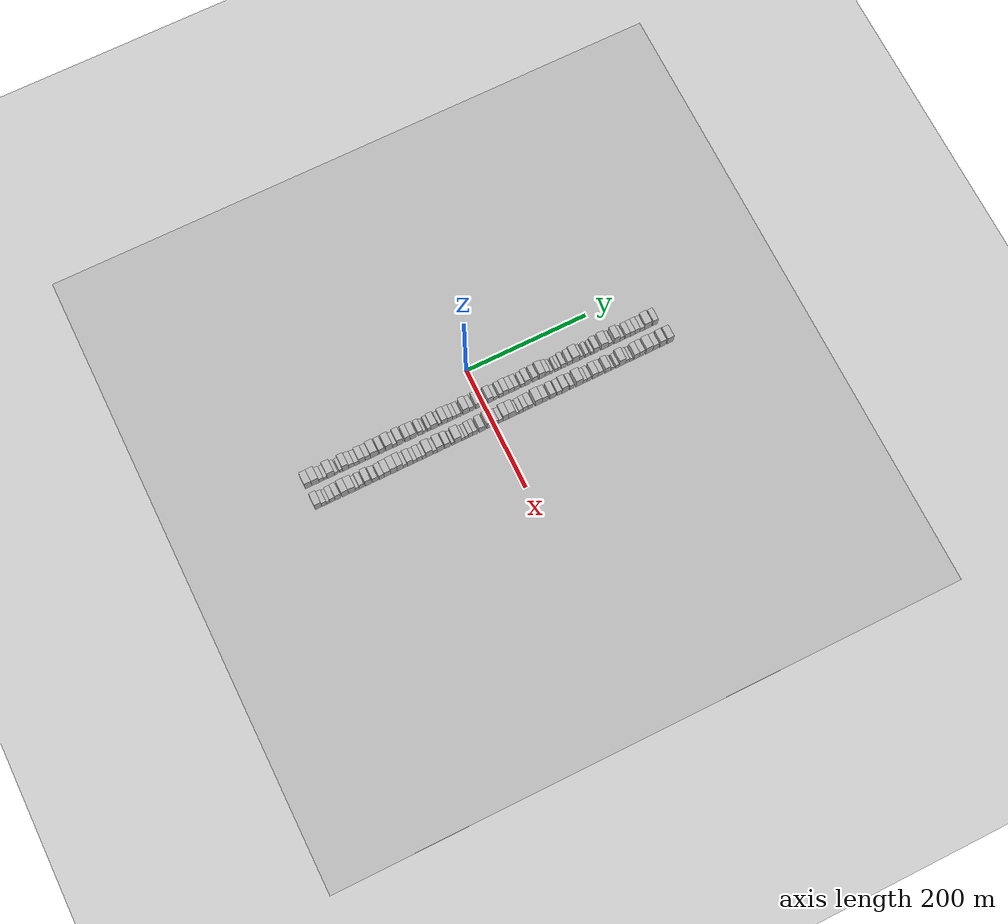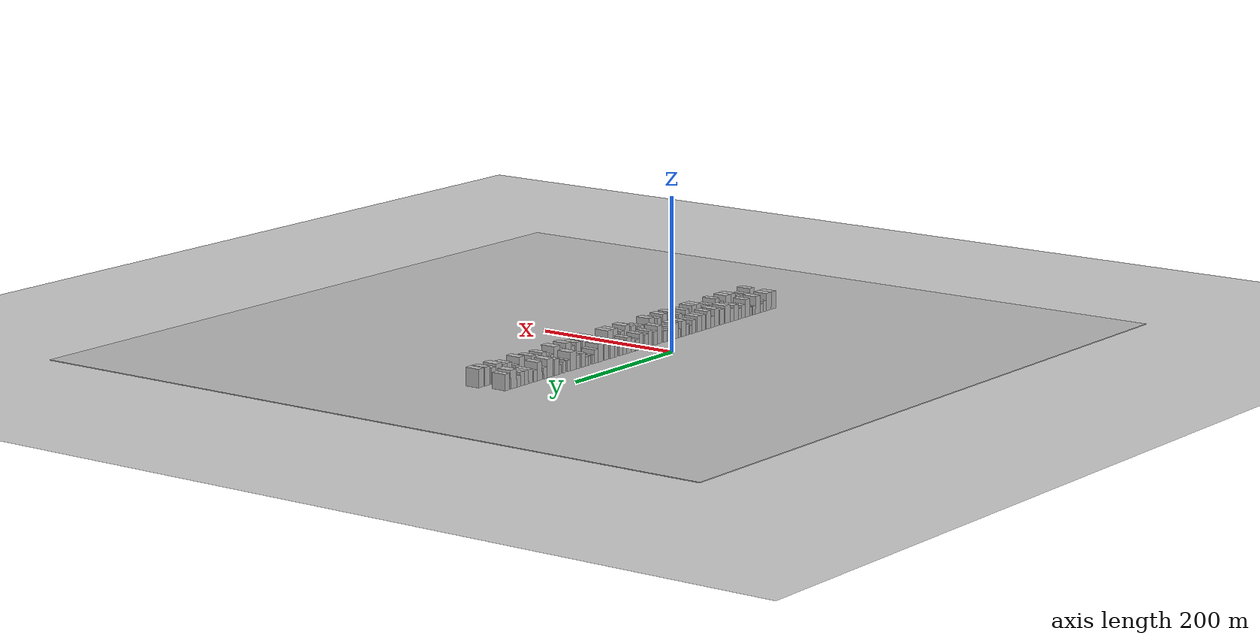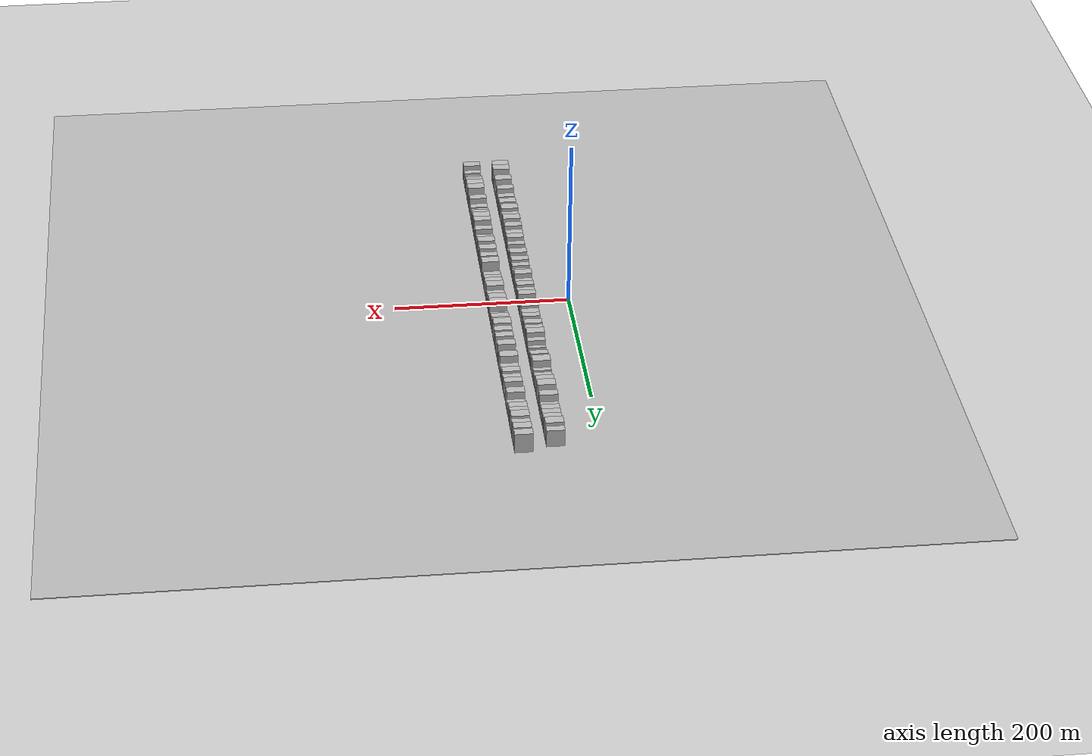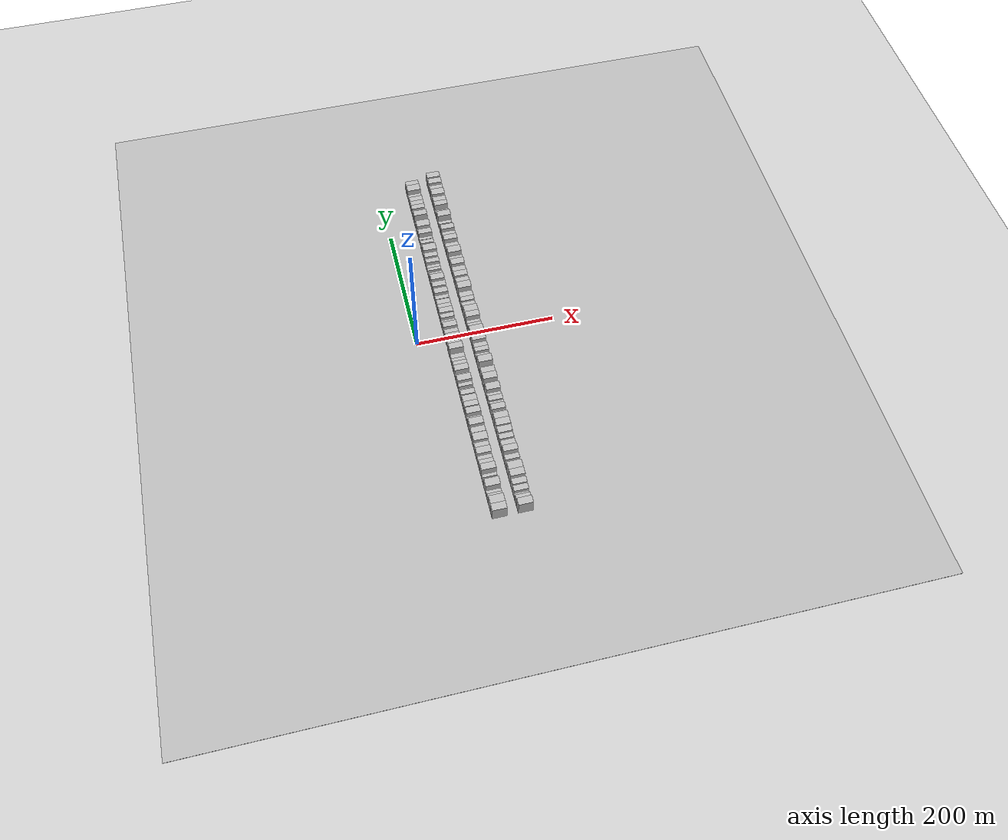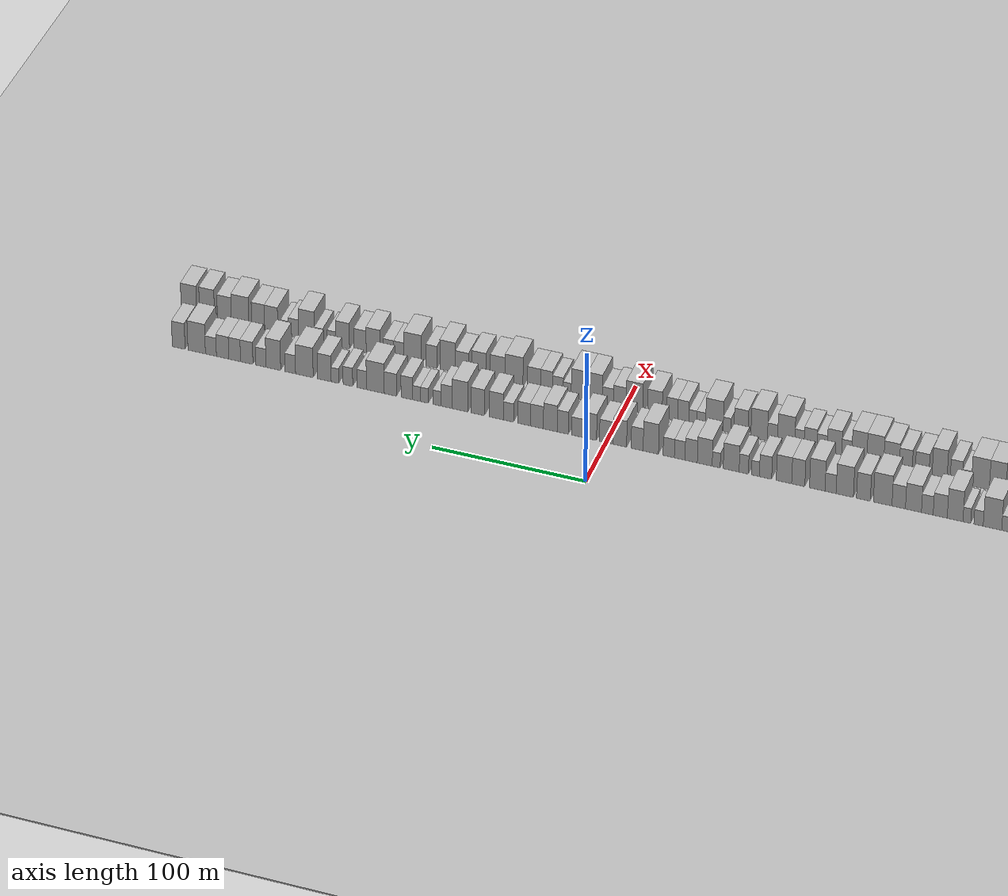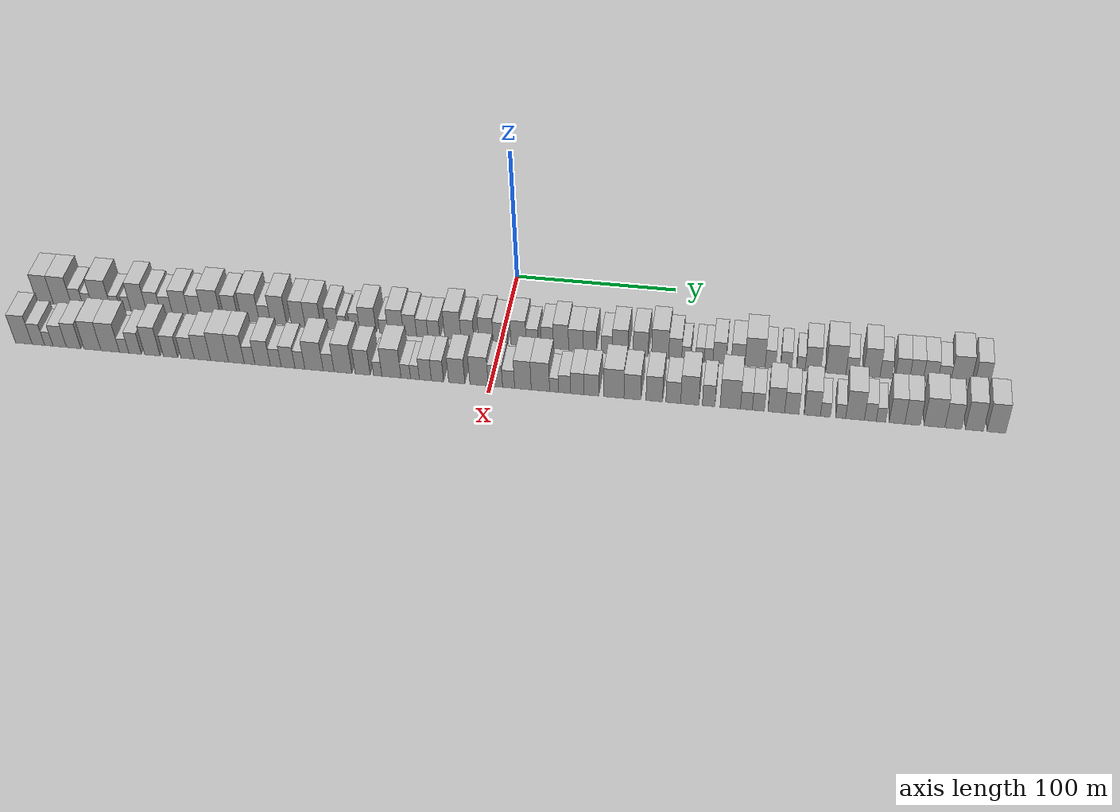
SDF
<?xml version="1.0" encoding="utf-8"?>

<sdf version="1.6">

   <world name="default">

      <gui fullscreen="0">

         <camera name="user_camera">

            <pose>-15 0 4.57585 0 0 0</pose>

            <view_controller>orbit</view_controller>

         </camera>

      </gui>

      <scene>

         <sky>

           <clouds>

             <speed>12</speed>

           </clouds>

         </sky>

         <ambient>0.4 0.4 0.4 1</ambient>

         <background>0.7 0.7 0.7 1</background>

         <shadows>1</shadows>

      </scene>

      <gravity>0 0 -9.8066</gravity>

      <magnetic_field>6e-06 2.3e-05 -4.2e-05</magnetic_field>

      <physics default="0" name="default_physics" type="ode">

         <ode>

            <solver>

               <type>quick</type>

               <iters>10</iters>

               <sor>1.0</sor>

               <use_dynamic_moi_rescaling>0</use_dynamic_moi_rescaling>

            </solver>

            <constraints>

               <cfm>0</cfm>

               <erp>0.2</erp>

               <contact_max_correcting_vel>100</contact_max_correcting_vel>

               <contact_surface_layer>0.001</contact_surface_layer>

            </constraints>

         </ode>

         <max_step_size>0.004</max_step_size>

         <real_time_factor>1</real_time_factor>

         <real_time_update_rate>250</real_time_update_rate>

      </physics>

      <light name="sun" type="directional">

         <cast_shadows>1</cast_shadows>

         <pose>0 0 10 0 0 0</pose>

         <diffuse>0.8 0.8 0.8 1</diffuse>

         <specular>0.2 0.2 0.2 1</specular>

         <attenuation>

            <range>1000</range>

            <constant>0.9</constant>

            <linear>0.01</linear>

            <quadratic>0.001</quadratic>

         </attenuation>

         <direction>-0.5 0.1 -0.9</direction>

      </light>

      <include>

         <name>ground_plane_1</name>

         <uri>model://HANNAS_ground_plane</uri>

         <pose>0 0 0  0 0 0</pose>

      </include>

      <include>

         <name>ground_plane_2</name>

         <uri>model://HANNAS_ground_plane</uri>

         <pose>100 0 0  0 0 0</pose>

      </include>

      <model name="building_1">

         <static>1</static>

         <pose frame="">50.0000 -284.7026 0 0.000000 0.000000 0.000000</pose>

         <link name="link">

            <pose frame="">0 0 12.00 0 0 0</pose>

            <collision name="collision">

               <geometry>

                  <box>

                     <size>20.0000 10.5947 24.0000</size>

                  </box>

               </geometry>

               <max_contacts>10</max_contacts>

               <surface>

                  <contact>

                     <ode/>

                  </contact>

                  <bounce/>

                  <friction>

                     <torsional>

                        <ode/>

                     </torsional>

                     <ode/>

                  </friction>

               </surface>

            </collision>

            <visual name="visual">

               <cast_shadows>0</cast_shadows>

               <geometry>

                  <box>

                     <size>20.0000 10.5947 24.0000</size>

                  </box>

               </geometry>

               <material>

                  <script>

                     <uri>model://HANNAS_wall/materials/scripts</uri>

                     <uri>model://HANNAS_wall/materials/textures</uri>

                     <name>vrc/HANNAS_wall</name>

                  </script>

               </material>

            </visual>

            <self_collide>0</self_collide>

            <enable_wind>0</enable_wind>

            <kinematic>0</kinematic>

         </link>

      </model>

      <model name="building_2">

         <static>1</static>

         <pose frame="">50.0000 -273.5966 0 0.000000 0.000000 0.000000</pose>

         <link name="link">

            <pose frame="">0 0 12.00 0 0 0</pose>

            <collision name="collision">

               <geometry>

                  <box>

                     <size>20.0000 11.6172 24.0000</size>

                  </box>

               </geometry>

               <max_contacts>10</max_contacts>

               <surface>

                  <contact>

                     <ode/>

                  </contact>

                  <bounce/>

                  <friction>

                     <torsional>

                        <ode/>

                     </torsional>

                     <ode/>

                  </friction>

               </surface>

            </collision>

            <visual name="visual">

               <cast_shadows>0</cast_shadows>

               <geometry>

                  <box>

                     <size>20.0000 11.6172 24.0000</size>

                  </box>

               </geometry>

               <material>

                  <script>

                     <uri>model://HANNAS_wall/materials/scripts</uri>

                     <uri>model://HANNAS_wall/materials/textures</uri>

                     <name>vrc/HANNAS_wall</name>

                  </script>

               </material>

            </visual>

            <self_collide>0</self_collide>

            <enable_wind>0</enable_wind>

            <kinematic>0</kinematic>

         </link>

      </model>

      <model name="building_3">

         <static>1</static>

         <pose frame="">50.0000 -264.0849 0 0.000000 0.000000 0.000000</pose>

         <link name="link">

            <pose frame="">0 0 7.50 0 0 0</pose>

            <collision name="collision">

               <geometry>

                  <box>

                     <size>20.0000 7.4063 15.0000</size>

                  </box>

               </geometry>

               <max_contacts>10</max_contacts>

               <surface>

                  <contact>

                     <ode/>

                  </contact>

                  <bounce/>

                  <friction>

                     <torsional>

                        <ode/>

                     </torsional>

                     <ode/>

                  </friction>

               </surface>

            </collision>

            <visual name="visual">

               <cast_shadows>0</cast_shadows>

               <geometry>

                  <box>

                     <size>20.0000 7.4063 15.0000</size>

                  </box>

               </geometry>

               <material>

                  <script>

                     <uri>model://HANNAS_wall/materials/scripts</uri>

                     <uri>model://HANNAS_wall/materials/textures</uri>

                     <name>vrc/HANNAS_wall</name>

                  </script>

               </material>

            </visual>

            <self_collide>0</self_collide>

            <enable_wind>0</enable_wind>

            <kinematic>0</kinematic>

         </link>

      </model>

      <model name="building_4">

         <static>1</static>

         <pose frame="">50.0000 -257.4461 0 0.000000 0.000000 0.000000</pose>

         <link name="link">

            <pose frame="">0 0 6.00 0 0 0</pose>

            <collision name="collision">

               <geometry>

                  <box>

                     <size>20.0000 5.8713 12.0000</size>

                  </box>

               </geometry>

               <max_contacts>10</max_contacts>

               <surface>

                  <contact>

                     <ode/>

                  </contact>

                  <bounce/>

                  <friction>

                     <torsional>

                        <ode/>

                     </torsional>

                     <ode/>

                  </friction>

               </surface>

            </collision>

            <visual name="visual">

               <cast_shadows>0</cast_shadows>

               <geometry>

                  <box>

                     <size>20.0000 5.8713 12.0000</size>

                  </box>

               </geometry>

               <material>

                  <script>

                     <uri>model://HANNAS_wall/materials/scripts</uri>

                     <uri>model://HANNAS_wall/materials/textures</uri>

                     <name>vrc/HANNAS_wall</name>

                  </script>

               </material>

            </visual>

            <self_collide>0</self_collide>

            <enable_wind>0</enable_wind>

            <kinematic>0</kinematic>

         </link>

      </model>

      <model name="building_5">

         <static>1</static>

         <pose frame="">50.0000 -248.6617 0 0.000000 0.000000 0.000000</pose>

         <link name="link">

            <pose frame="">0 0 12.00 0 0 0</pose>

            <collision name="collision">

               <geometry>

                  <box>

                     <size>20.0000 11.6974 24.0000</size>

                  </box>

               </geometry>

               <max_contacts>10</max_contacts>

               <surface>

                  <contact>

                     <ode/>

                  </contact>

                  <bounce/>

                  <friction>

                     <torsional>

                        <ode/>

                     </torsional>

                     <ode/>

                  </friction>

               </surface>

            </collision>

            <visual name="visual">

               <cast_shadows>0</cast_shadows>

               <geometry>

                  <box>

                     <size>20.0000 11.6974 24.0000</size>

                  </box>

               </geometry>

               <material>

                  <script>

                     <uri>model://HANNAS_wall/materials/scripts</uri>

                     <uri>model://HANNAS_wall/materials/textures</uri>

                     <name>vrc/HANNAS_wall</name>

                  </script>

               </material>

            </visual>

            <self_collide>0</self_collide>

            <enable_wind>0</enable_wind>

            <kinematic>0</kinematic>

         </link>

      </model>

      <model name="building_6">

         <static>1</static>

         <pose frame="">50.0000 -239.8674 0 0.000000 0.000000 0.000000</pose>

         <link name="link">

            <pose frame="">0 0 6.00 0 0 0</pose>

            <collision name="collision">

               <geometry>

                  <box>

                     <size>20.0000 5.8914 12.0000</size>

                  </box>

               </geometry>

               <max_contacts>10</max_contacts>

               <surface>

                  <contact>

                     <ode/>

                  </contact>

                  <bounce/>

                  <friction>

                     <torsional>

                        <ode/>

                     </torsional>

                     <ode/>

                  </friction>

               </surface>

            </collision>

            <visual name="visual">

               <cast_shadows>0</cast_shadows>

               <geometry>

                  <box>

                     <size>20.0000 5.8914 12.0000</size>

                  </box>

               </geometry>

               <material>

                  <script>

                     <uri>model://HANNAS_wall/materials/scripts</uri>

                     <uri>model://HANNAS_wall/materials/textures</uri>

                     <name>vrc/HANNAS_wall</name>

                  </script>

               </material>

            </visual>

            <self_collide>0</self_collide>

            <enable_wind>0</enable_wind>

            <kinematic>0</kinematic>

         </link>

      </model>

      <model name="building_7">

         <static>1</static>

         <pose frame="">50.0000 -232.4474 0 0.000000 0.000000 0.000000</pose>

         <link name="link">

            <pose frame="">0 0 6.00 0 0 0</pose>

            <collision name="collision">

               <geometry>

                  <box>

                     <size>20.0000 4.9485 12.0000</size>

                  </box>

               </geometry>

               <max_contacts>10</max_contacts>

               <surface>

                  <contact>

                     <ode/>

                  </contact>

                  <bounce/>

                  <friction>

                     <torsional>

                        <ode/>

                     </torsional>

                     <ode/>

                  </friction>

               </surface>

            </collision>

            <visual name="visual">

               <cast_shadows>0</cast_shadows>

               <geometry>

                  <box>

                     <size>20.0000 4.9485 12.0000</size>

                  </box>

               </geometry>

               <material>

                  <script>

                     <uri>model://HANNAS_wall/materials/scripts</uri>

                     <uri>model://HANNAS_wall/materials/textures</uri>

                     <name>vrc/HANNAS_wall</name>

                  </script>

               </material>

            </visual>

            <self_collide>0</self_collide>

            <enable_wind>0</enable_wind>

            <kinematic>0</kinematic>

         </link>

      </model>

      <model name="building_8">

         <static>1</static>

         <pose frame="">50.0000 -224.9844 0 0.000000 0.000000 0.000000</pose>

         <link name="link">

            <pose frame="">0 0 12.00 0 0 0</pose>

            <collision name="collision">

               <geometry>

                  <box>

                     <size>20.0000 9.9776 24.0000</size>

                  </box>

               </geometry>

               <max_contacts>10</max_contacts>

               <surface>

                  <contact>

                     <ode/>

                  </contact>

                  <bounce/>

                  <friction>

                     <torsional>

                        <ode/>

                     </torsional>

                     <ode/>

                  </friction>

               </surface>

            </collision>

            <visual name="visual">

               <cast_shadows>0</cast_shadows>

               <geometry>

                  <box>

                     <size>20.0000 9.9776 24.0000</size>

                  </box>

               </geometry>

               <material>

                  <script>

                     <uri>model://HANNAS_wall/materials/scripts</uri>

                     <uri>model://HANNAS_wall/materials/textures</uri>

                     <name>vrc/HANNAS_wall</name>

                  </script>

               </material>

            </visual>

            <self_collide>0</self_collide>

            <enable_wind>0</enable_wind>

            <kinematic>0</kinematic>

         </link>

      </model>

      <model name="building_9">

         <static>1</static>

         <pose frame="">50.0000 -215.5335 0 0.000000 0.000000 0.000000</pose>

         <link name="link">

            <pose frame="">0 0 9.00 0 0 0</pose>

            <collision name="collision">

               <geometry>

                  <box>

                     <size>20.0000 8.9242 18.0000</size>

                  </box>

               </geometry>

               <max_contacts>10</max_contacts>

               <surface>

                  <contact>

                     <ode/>

                  </contact>

                  <bounce/>

                  <friction>

                     <torsional>

                        <ode/>

                     </torsional>

                     <ode/>

                  </friction>

               </surface>

            </collision>

            <visual name="visual">

               <cast_shadows>0</cast_shadows>

               <geometry>

                  <box>

                     <size>20.0000 8.9242 18.0000</size>

                  </box>

               </geometry>

               <material>

                  <script>

                     <uri>model://HANNAS_wall/materials/scripts</uri>

                     <uri>model://HANNAS_wall/materials/textures</uri>

                     <name>vrc/HANNAS_wall</name>

                  </script>

               </material>

            </visual>

            <self_collide>0</self_collide>

            <enable_wind>0</enable_wind>

            <kinematic>0</kinematic>

         </link>

      </model>

      <model name="building_10">

         <static>1</static>

         <pose frame="">50.0000 -207.3426 0 0.000000 0.000000 0.000000</pose>

         <link name="link">

            <pose frame="">0 0 7.50 0 0 0</pose>

            <collision name="collision">

               <geometry>

                  <box>

                     <size>20.0000 7.4575 15.0000</size>

                  </box>

               </geometry>

               <max_contacts>10</max_contacts>

               <surface>

                  <contact>

                     <ode/>

                  </contact>

                  <bounce/>

                  <friction>

                     <torsional>

                        <ode/>

                     </torsional>

                     <ode/>

                  </friction>

               </surface>

            </collision>

            <visual name="visual">

               <cast_shadows>0</cast_shadows>

               <geometry>

                  <box>

                     <size>20.0000 7.4575 15.0000</size>

                  </box>

               </geometry>

               <material>

                  <script>

                     <uri>model://HANNAS_wall/materials/scripts</uri>

                     <uri>model://HANNAS_wall/materials/textures</uri>

                     <name>vrc/HANNAS_wall</name>

                  </script>

               </material>

            </visual>

            <self_collide>0</self_collide>

            <enable_wind>0</enable_wind>

            <kinematic>0</kinematic>

         </link>

      </model>

      <model name="building_11">

         <static>1</static>

         <pose frame="">50.0000 -198.5121 0 0.000000 0.000000 0.000000</pose>

         <link name="link">

            <pose frame="">0 0 10.50 0 0 0</pose>

            <collision name="collision">

               <geometry>

                  <box>

                     <size>20.0000 10.2037 21.0000</size>

                  </box>

               </geometry>

               <max_contacts>10</max_contacts>

               <surface>

                  <contact>

                     <ode/>

                  </contact>

                  <bounce/>

                  <friction>

                     <torsional>

                        <ode/>

                     </torsional>

                     <ode/>

                  </friction>

               </surface>

            </collision>

            <visual name="visual">

               <cast_shadows>0</cast_shadows>

               <geometry>

                  <box>

                     <size>20.0000 10.2037 21.0000</size>

                  </box>

               </geometry>

               <material>

                  <script>

                     <uri>model://HANNAS_wall/materials/scripts</uri>

                     <uri>model://HANNAS_wall/materials/textures</uri>

                     <name>vrc/HANNAS_wall</name>

                  </script>

               </material>

            </visual>

            <self_collide>0</self_collide>

            <enable_wind>0</enable_wind>

            <kinematic>0</kinematic>

         </link>

      </model>

      <model name="building_12">

         <static>1</static>

         <pose frame="">50.0000 -189.1027 0 0.000000 0.000000 0.000000</pose>

         <link name="link">

            <pose frame="">0 0 9.00 0 0 0</pose>

            <collision name="collision">

               <geometry>

                  <box>

                     <size>20.0000 8.6149 18.0000</size>

                  </box>

               </geometry>

               <max_contacts>10</max_contacts>

               <surface>

                  <contact>

                     <ode/>

                  </contact>

                  <bounce/>

                  <friction>

                     <torsional>

                        <ode/>

                     </torsional>

                     <ode/>

                  </friction>

               </surface>

            </collision>

            <visual name="visual">

               <cast_shadows>0</cast_shadows>

               <geometry>

                  <box>

                     <size>20.0000 8.6149 18.0000</size>

                  </box>

               </geometry>

               <material>

                  <script>

                     <uri>model://HANNAS_wall/materials/scripts</uri>

                     <uri>model://HANNAS_wall/materials/textures</uri>

                     <name>vrc/HANNAS_wall</name>

                  </script>

               </material>

            </visual>

            <self_collide>0</self_collide>

            <enable_wind>0</enable_wind>

            <kinematic>0</kinematic>

         </link>

      </model>

      <model name="building_13">

         <static>1</static>

         <pose frame="">50.0000 -178.8727 0 0.000000 0.000000 0.000000</pose>

         <link name="link">

            <pose frame="">0 0 12.00 0 0 0</pose>

            <collision name="collision">

               <geometry>

                  <box>

                     <size>20.0000 11.8451 24.0000</size>

                  </box>

               </geometry>

               <max_contacts>10</max_contacts>

               <surface>

                  <contact>

                     <ode/>

                  </contact>

                  <bounce/>

                  <friction>

                     <torsional>

                        <ode/>

                     </torsional>

                     <ode/>

                  </friction>

               </surface>

            </collision>

            <visual name="visual">

               <cast_shadows>0</cast_shadows>

               <geometry>

                  <box>

                     <size>20.0000 11.8451 24.0000</size>

                  </box>

               </geometry>

               <material>

                  <script>

                     <uri>model://HANNAS_wall/materials/scripts</uri>

                     <uri>model://HANNAS_wall/materials/textures</uri>

                     <name>vrc/HANNAS_wall</name>

                  </script>

               </material>

            </visual>

            <self_collide>0</self_collide>

            <enable_wind>0</enable_wind>

            <kinematic>0</kinematic>

         </link>

      </model>

      <model name="building_14">

         <static>1</static>

         <pose frame="">50.0000 -166.5378 0 0.000000 0.000000 0.000000</pose>

         <link name="link">

            <pose frame="">0 0 10.50 0 0 0</pose>

            <collision name="collision">

               <geometry>

                  <box>

                     <size>20.0000 8.8249 21.0000</size>

                  </box>

               </geometry>

               <max_contacts>10</max_contacts>

               <surface>

                  <contact>

                     <ode/>

                  </contact>

                  <bounce/>

                  <friction>

                     <torsional>

                        <ode/>

                     </torsional>

                     <ode/>

                  </friction>

               </surface>

            </collision>

            <visual name="visual">

               <cast_shadows>0</cast_shadows>

               <geometry>

                  <box>

                     <size>20.0000 8.8249 21.0000</size>

                  </box>

               </geometry>

               <material>

                  <script>

                     <uri>model://HANNAS_wall/materials/scripts</uri>

                     <uri>model://HANNAS_wall/materials/textures</uri>

                     <name>vrc/HANNAS_wall</name>

                  </script>

               </material>

            </visual>

            <self_collide>0</self_collide>

            <enable_wind>0</enable_wind>

            <kinematic>0</kinematic>

         </link>

      </model>

      <model name="building_15">

         <static>1</static>

         <pose frame="">50.0000 -154.5810 0 0.000000 0.000000 0.000000</pose>

         <link name="link">

            <pose frame="">0 0 12.00 0 0 0</pose>

            <collision name="collision">

               <geometry>

                  <box>

                     <size>20.0000 11.0885 24.0000</size>

                  </box>

               </geometry>

               <max_contacts>10</max_contacts>

               <surface>

                  <contact>

                     <ode/>

                  </contact>

                  <bounce/>

                  <friction>

                     <torsional>

                        <ode/>

                     </torsional>

                     <ode/>

                  </friction>

               </surface>

            </collision>

            <visual name="visual">

               <cast_shadows>0</cast_shadows>

               <geometry>

                  <box>

                     <size>20.0000 11.0885 24.0000</size>

                  </box>

               </geometry>

               <material>

                  <script>

                     <uri>model://HANNAS_wall/materials/scripts</uri>

                     <uri>model://HANNAS_wall/materials/textures</uri>

                     <name>vrc/HANNAS_wall</name>

                  </script>

               </material>

            </visual>

            <self_collide>0</self_collide>

            <enable_wind>0</enable_wind>

            <kinematic>0</kinematic>

         </link>

      </model>

      <model name="building_16">

         <static>1</static>

         <pose frame="">50.0000 -145.4833 0 0.000000 0.000000 0.000000</pose>

         <link name="link">

            <pose frame="">0 0 7.50 0 0 0</pose>

            <collision name="collision">

               <geometry>

                  <box>

                     <size>20.0000 7.1070 15.0000</size>

                  </box>

               </geometry>

               <max_contacts>10</max_contacts>

               <surface>

                  <contact>

                     <ode/>

                  </contact>

                  <bounce/>

                  <friction>

                     <torsional>

                        <ode/>

                     </torsional>

                     <ode/>

                  </friction>

               </surface>

            </collision>

            <visual name="visual">

               <cast_shadows>0</cast_shadows>

               <geometry>

                  <box>

                     <size>20.0000 7.1070 15.0000</size>

                  </box>

               </geometry>

               <material>

                  <script>

                     <uri>model://HANNAS_wall/materials/scripts</uri>

                     <uri>model://HANNAS_wall/materials/textures</uri>

                     <name>vrc/HANNAS_wall</name>

                  </script>

               </material>

            </visual>

            <self_collide>0</self_collide>

            <enable_wind>0</enable_wind>

            <kinematic>0</kinematic>

         </link>

      </model>

      <model name="building_17">

         <static>1</static>

         <pose frame="">50.0000 -136.9539 0 0.000000 0.000000 0.000000</pose>

         <link name="link">

            <pose frame="">0 0 12.00 0 0 0</pose>

            <collision name="collision">

               <geometry>

                  <box>

                     <size>20.0000 9.9518 24.0000</size>

                  </box>

               </geometry>

               <max_contacts>10</max_contacts>

               <surface>

                  <contact>

                     <ode/>

                  </contact>

                  <bounce/>

                  <friction>

                     <torsional>

                        <ode/>

                     </torsional>

                     <ode/>

                  </friction>

               </surface>

            </collision>

            <visual name="visual">

               <cast_shadows>0</cast_shadows>

               <geometry>

                  <box>

                     <size>20.0000 9.9518 24.0000</size>

                  </box>

               </geometry>

               <material>

                  <script>

                     <uri>model://HANNAS_wall/materials/scripts</uri>

                     <uri>model://HANNAS_wall/materials/textures</uri>

                     <name>vrc/HANNAS_wall</name>

                  </script>

               </material>

            </visual>

            <self_collide>0</self_collide>

            <enable_wind>0</enable_wind>

            <kinematic>0</kinematic>

         </link>

      </model>

      <model name="building_18">

         <static>1</static>

         <pose frame="">50.0000 -124.7235 0 0.000000 0.000000 0.000000</pose>

         <link name="link">

            <pose frame="">0 0 10.50 0 0 0</pose>

            <collision name="collision">

               <geometry>

                  <box>

                     <size>20.0000 8.5091 21.0000</size>

                  </box>

               </geometry>

               <max_contacts>10</max_contacts>

               <surface>

                  <contact>

                     <ode/>

                  </contact>

                  <bounce/>

                  <friction>

                     <torsional>

                        <ode/>

                     </torsional>

                     <ode/>

                  </friction>

               </surface>

            </collision>

            <visual name="visual">

               <cast_shadows>0</cast_shadows>

               <geometry>

                  <box>

                     <size>20.0000 8.5091 21.0000</size>

                  </box>

               </geometry>

               <material>

                  <script>

                     <uri>model://HANNAS_wall/materials/scripts</uri>

                     <uri>model://HANNAS_wall/materials/textures</uri>

                     <name>vrc/HANNAS_wall</name>

                  </script>

               </material>

            </visual>

            <self_collide>0</self_collide>

            <enable_wind>0</enable_wind>

            <kinematic>0</kinematic>

         </link>

      </model>

      <model name="building_19">

         <static>1</static>

         <pose frame="">50.0000 -115.5313 0 0.000000 0.000000 0.000000</pose>

         <link name="link">

            <pose frame="">0 0 10.50 0 0 0</pose>

            <collision name="collision">

               <geometry>

                  <box>

                     <size>20.0000 9.8753 21.0000</size>

                  </box>

               </geometry>

               <max_contacts>10</max_contacts>

               <surface>

                  <contact>

                     <ode/>

                  </contact>

                  <bounce/>

                  <friction>

                     <torsional>

                        <ode/>

                     </torsional>

                     <ode/>

                  </friction>

               </surface>

            </collision>

            <visual name="visual">

               <cast_shadows>0</cast_shadows>

               <geometry>

                  <box>

                     <size>20.0000 9.8753 21.0000</size>

                  </box>

               </geometry>

               <material>

                  <script>

                     <uri>model://HANNAS_wall/materials/scripts</uri>

                     <uri>model://HANNAS_wall/materials/textures</uri>

                     <name>vrc/HANNAS_wall</name>

                  </script>

               </material>

            </visual>

            <self_collide>0</self_collide>

            <enable_wind>0</enable_wind>

            <kinematic>0</kinematic>

         </link>

      </model>

      <model name="building_20">

         <static>1</static>

         <pose frame="">50.0000 -103.6340 0 0.000000 0.000000 0.000000</pose>

         <link name="link">

            <pose frame="">0 0 9.00 0 0 0</pose>

            <collision name="collision">

               <geometry>

                  <box>

                     <size>20.0000 7.9193 18.0000</size>

                  </box>

               </geometry>

               <max_contacts>10</max_contacts>

               <surface>

                  <contact>

                     <ode/>

                  </contact>

                  <bounce/>

                  <friction>

                     <torsional>

                        <ode/>

                     </torsional>

                     <ode/>

                  </friction>

               </surface>

            </collision>

            <visual name="visual">

               <cast_shadows>0</cast_shadows>

               <geometry>

                  <box>

                     <size>20.0000 7.9193 18.0000</size>

                  </box>

               </geometry>

               <material>

                  <script>

                     <uri>model://HANNAS_wall/materials/scripts</uri>

                     <uri>model://HANNAS_wall/materials/textures</uri>

                     <name>vrc/HANNAS_wall</name>

                  </script>

               </material>

            </visual>

            <self_collide>0</self_collide>

            <enable_wind>0</enable_wind>

            <kinematic>0</kinematic>

         </link>

      </model>

      <model name="building_21">

         <static>1</static>

         <pose frame="">50.0000 -97.1221 0 0.000000 0.000000 0.000000</pose>

         <link name="link">

            <pose frame="">0 0 6.00 0 0 0</pose>

            <collision name="collision">

               <geometry>

                  <box>

                     <size>20.0000 5.1045 12.0000</size>

                  </box>

               </geometry>

               <max_contacts>10</max_contacts>

               <surface>

                  <contact>

                     <ode/>

                  </contact>

                  <bounce/>

                  <friction>

                     <torsional>

                        <ode/>

                     </torsional>

                     <ode/>

                  </friction>

               </surface>

            </collision>

            <visual name="visual">

               <cast_shadows>0</cast_shadows>

               <geometry>

                  <box>

                     <size>20.0000 5.1045 12.0000</size>

                  </box>

               </geometry>

               <material>

                  <script>

                     <uri>model://HANNAS_wall/materials/scripts</uri>

                     <uri>model://HANNAS_wall/materials/textures</uri>

                     <name>vrc/HANNAS_wall</name>

                  </script>

               </material>

            </visual>

            <self_collide>0</self_collide>

            <enable_wind>0</enable_wind>

            <kinematic>0</kinematic>

         </link>

      </model>

      <model name="building_22">

         <static>1</static>

         <pose frame="">50.0000 -89.5682 0 0.000000 0.000000 0.000000</pose>

         <link name="link">

            <pose frame="">0 0 7.50 0 0 0</pose>

            <collision name="collision">

               <geometry>

                  <box>

                     <size>20.0000 6.0033 15.0000</size>

                  </box>

               </geometry>

               <max_contacts>10</max_contacts>

               <surface>

                  <contact>

                     <ode/>

                  </contact>

                  <bounce/>

                  <friction>

                     <torsional>

                        <ode/>

                     </torsional>

                     <ode/>

                  </friction>

               </surface>

            </collision>

            <visual name="visual">

               <cast_shadows>0</cast_shadows>

               <geometry>

                  <box>

                     <size>20.0000 6.0033 15.0000</size>

                  </box>

               </geometry>

               <material>

                  <script>

                     <uri>model://HANNAS_wall/materials/scripts</uri>

                     <uri>model://HANNAS_wall/materials/textures</uri>

                     <name>vrc/HANNAS_wall</name>

                  </script>

               </material>

            </visual>

            <self_collide>0</self_collide>

            <enable_wind>0</enable_wind>

            <kinematic>0</kinematic>

         </link>

      </model>

      <model name="building_23">

         <static>1</static>

         <pose frame="">50.0000 -81.4354 0 0.000000 0.000000 0.000000</pose>

         <link name="link">

            <pose frame="">0 0 10.50 0 0 0</pose>

            <collision name="collision">

               <geometry>

                  <box>

                     <size>20.0000 10.2623 21.0000</size>

                  </box>

               </geometry>

               <max_contacts>10</max_contacts>

               <surface>

                  <contact>

                     <ode/>

                  </contact>

                  <bounce/>

                  <friction>

                     <torsional>

                        <ode/>

                     </torsional>

                     <ode/>

                  </friction>

               </surface>

            </collision>

            <visual name="visual">

               <cast_shadows>0</cast_shadows>

               <geometry>

                  <box>

                     <size>20.0000 10.2623 21.0000</size>

                  </box>

               </geometry>

               <material>

                  <script>

                     <uri>model://HANNAS_wall/materials/scripts</uri>

                     <uri>model://HANNAS_wall/materials/textures</uri>

                     <name>vrc/HANNAS_wall</name>

                  </script>

               </material>

            </visual>

            <self_collide>0</self_collide>

            <enable_wind>0</enable_wind>

            <kinematic>0</kinematic>

         </link>

      </model>

      <model name="building_24">

         <static>1</static>

         <pose frame="">50.0000 -71.7122 0 0.000000 0.000000 0.000000</pose>

         <link name="link">

            <pose frame="">0 0 6.00 0 0 0</pose>

            <collision name="collision">

               <geometry>

                  <box>

                     <size>20.0000 5.1841 12.0000</size>

                  </box>

               </geometry>

               <max_contacts>10</max_contacts>

               <surface>

                  <contact>

                     <ode/>

                  </contact>

                  <bounce/>

                  <friction>

                     <torsional>

                        <ode/>

                     </torsional>

                     <ode/>

                  </friction>

               </surface>

            </collision>

            <visual name="visual">

               <cast_shadows>0</cast_shadows>

               <geometry>

                  <box>

                     <size>20.0000 5.1841 12.0000</size>

                  </box>

               </geometry>

               <material>

                  <script>

                     <uri>model://HANNAS_wall/materials/scripts</uri>

                     <uri>model://HANNAS_wall/materials/textures</uri>

                     <name>vrc/HANNAS_wall</name>

                  </script>

               </material>

            </visual>

            <self_collide>0</self_collide>

            <enable_wind>0</enable_wind>

            <kinematic>0</kinematic>

         </link>

      </model>

      <model name="building_25">

         <static>1</static>

         <pose frame="">50.0000 -64.2973 0 0.000000 0.000000 0.000000</pose>

         <link name="link">

            <pose frame="">0 0 10.50 0 0 0</pose>

            <collision name="collision">

               <geometry>

                  <box>

                     <size>20.0000 9.6455 21.0000</size>

                  </box>

               </geometry>

               <max_contacts>10</max_contacts>

               <surface>

                  <contact>

                     <ode/>

                  </contact>

                  <bounce/>

                  <friction>

                     <torsional>

                        <ode/>

                     </torsional>

                     <ode/>

                  </friction>

               </surface>

            </collision>

            <visual name="visual">

               <cast_shadows>0</cast_shadows>

               <geometry>

                  <box>

                     <size>20.0000 9.6455 21.0000</size>

                  </box>

               </geometry>

               <material>

                  <script>

                     <uri>model://HANNAS_wall/materials/scripts</uri>

                     <uri>model://HANNAS_wall/materials/textures</uri>

                     <name>vrc/HANNAS_wall</name>

                  </script>

               </material>

            </visual>

            <self_collide>0</self_collide>

            <enable_wind>0</enable_wind>

            <kinematic>0</kinematic>

         </link>

      </model>

      <model name="building_26">

         <static>1</static>

         <pose frame="">50.0000 -55.4743 0 0.000000 0.000000 0.000000</pose>

         <link name="link">

            <pose frame="">0 0 9.00 0 0 0</pose>

            <collision name="collision">

               <geometry>

                  <box>

                     <size>20.0000 8.0005 18.0000</size>

                  </box>

               </geometry>

               <max_contacts>10</max_contacts>

               <surface>

                  <contact>

                     <ode/>

                  </contact>

                  <bounce/>

                  <friction>

                     <torsional>

                        <ode/>

                     </torsional>

                     <ode/>

                  </friction>

               </surface>

            </collision>

            <visual name="visual">

               <cast_shadows>0</cast_shadows>

               <geometry>

                  <box>

                     <size>20.0000 8.0005 18.0000</size>

                  </box>

               </geometry>

               <material>

                  <script>

                     <uri>model://HANNAS_wall/materials/scripts</uri>

                     <uri>model://HANNAS_wall/materials/textures</uri>

                     <name>vrc/HANNAS_wall</name>

                  </script>

               </material>

            </visual>

            <self_collide>0</self_collide>

            <enable_wind>0</enable_wind>

            <kinematic>0</kinematic>

         </link>

      </model>

      <model name="building_27">

         <static>1</static>

         <pose frame="">50.0000 -47.9953 0 0.000000 0.000000 0.000000</pose>

         <link name="link">

            <pose frame="">0 0 7.50 0 0 0</pose>

            <collision name="collision">

               <geometry>

                  <box>

                     <size>20.0000 6.9575 15.0000</size>

                  </box>

               </geometry>

               <max_contacts>10</max_contacts>

               <surface>

                  <contact>

                     <ode/>

                  </contact>

                  <bounce/>

                  <friction>

                     <torsional>

                        <ode/>

                     </torsional>

                     <ode/>

                  </friction>

               </surface>

            </collision>

            <visual name="visual">

               <cast_shadows>0</cast_shadows>

               <geometry>

                  <box>

                     <size>20.0000 6.9575 15.0000</size>

                  </box>

               </geometry>

               <material>

                  <script>

                     <uri>model://HANNAS_wall/materials/scripts</uri>

                     <uri>model://HANNAS_wall/materials/textures</uri>

                     <name>vrc/HANNAS_wall</name>

                  </script>

               </material>

            </visual>

            <self_collide>0</self_collide>

            <enable_wind>0</enable_wind>

            <kinematic>0</kinematic>

         </link>

      </model>

      <model name="building_28">

         <static>1</static>

         <pose frame="">50.0000 -40.8460 0 0.000000 0.000000 0.000000</pose>

         <link name="link">

            <pose frame="">0 0 7.50 0 0 0</pose>

            <collision name="collision">

               <geometry>

                  <box>

                     <size>20.0000 7.3411 15.0000</size>

                  </box>

               </geometry>

               <max_contacts>10</max_contacts>

               <surface>

                  <contact>

                     <ode/>

                  </contact>

                  <bounce/>

                  <friction>

                     <torsional>

                        <ode/>

                     </torsional>

                     <ode/>

                  </friction>

               </surface>

            </collision>

            <visual name="visual">

               <cast_shadows>0</cast_shadows>

               <geometry>

                  <box>

                     <size>20.0000 7.3411 15.0000</size>

                  </box>

               </geometry>

               <material>

                  <script>

                     <uri>model://HANNAS_wall/materials/scripts</uri>

                     <uri>model://HANNAS_wall/materials/textures</uri>

                     <name>vrc/HANNAS_wall</name>

                  </script>

               </material>

            </visual>

            <self_collide>0</self_collide>

            <enable_wind>0</enable_wind>

            <kinematic>0</kinematic>

         </link>

      </model>

      <model name="building_29">

         <static>1</static>

         <pose frame="">50.0000 -29.1868 0 0.000000 0.000000 0.000000</pose>

         <link name="link">

            <pose frame="">0 0 12.00 0 0 0</pose>

            <collision name="collision">

               <geometry>

                  <box>

                     <size>20.0000 9.9773 24.0000</size>

                  </box>

               </geometry>

               <max_contacts>10</max_contacts>

               <surface>

                  <contact>

                     <ode/>

                  </contact>

                  <bounce/>

                  <friction>

                     <torsional>

                        <ode/>

                     </torsional>

                     <ode/>

                  </friction>

               </surface>

            </collision>

            <visual name="visual">

               <cast_shadows>0</cast_shadows>

               <geometry>

                  <box>

                     <size>20.0000 9.9773 24.0000</size>

                  </box>

               </geometry>

               <material>

                  <script>

                     <uri>model://HANNAS_wall/materials/scripts</uri>

                     <uri>model://HANNAS_wall/materials/textures</uri>

                     <name>vrc/HANNAS_wall</name>

                  </script>

               </material>

            </visual>

            <self_collide>0</self_collide>

            <enable_wind>0</enable_wind>

            <kinematic>0</kinematic>

         </link>

      </model>

      <model name="building_30">

         <static>1</static>

         <pose frame="">50.0000 -20.2898 0 0.000000 0.000000 0.000000</pose>

         <link name="link">

            <pose frame="">0 0 9.00 0 0 0</pose>

            <collision name="collision">

               <geometry>

                  <box>

                     <size>20.0000 7.8167 18.0000</size>

                  </box>

               </geometry>

               <max_contacts>10</max_contacts>

               <surface>

                  <contact>

                     <ode/>

                  </contact>

                  <bounce/>

                  <friction>

                     <torsional>

                        <ode/>

                     </torsional>

                     <ode/>

                  </friction>

               </surface>

            </collision>

            <visual name="visual">

               <cast_shadows>0</cast_shadows>

               <geometry>

                  <box>

                     <size>20.0000 7.8167 18.0000</size>

                  </box>

               </geometry>

               <material>

                  <script>

                     <uri>model://HANNAS_wall/materials/scripts</uri>

                     <uri>model://HANNAS_wall/materials/textures</uri>

                     <name>vrc/HANNAS_wall</name>

                  </script>

               </material>

            </visual>

            <self_collide>0</self_collide>

            <enable_wind>0</enable_wind>

            <kinematic>0</kinematic>

         </link>

      </model>

      <model name="building_31">

         <static>1</static>

         <pose frame="">50.0000 -8.9502 0 0.000000 0.000000 0.000000</pose>

         <link name="link">

            <pose frame="">0 0 10.50 0 0 0</pose>

            <collision name="collision">

               <geometry>

                  <box>

                     <size>20.0000 8.8623 21.0000</size>

                  </box>

               </geometry>

               <max_contacts>10</max_contacts>

               <surface>

                  <contact>

                     <ode/>

                  </contact>

                  <bounce/>

                  <friction>

                     <torsional>

                        <ode/>

                     </torsional>

                     <ode/>

                  </friction>

               </surface>

            </collision>

            <visual name="visual">

               <cast_shadows>0</cast_shadows>

               <geometry>

                  <box>

                     <size>20.0000 8.8623 21.0000</size>

                  </box>

               </geometry>

               <material>

                  <script>

                     <uri>model://HANNAS_wall/materials/scripts</uri>

                     <uri>model://HANNAS_wall/materials/textures</uri>

                     <name>vrc/HANNAS_wall</name>

                  </script>

               </material>

            </visual>

            <self_collide>0</self_collide>

            <enable_wind>0</enable_wind>

            <kinematic>0</kinematic>

         </link>

      </model>

      <model name="building_32">

         <static>1</static>

         <pose frame="">50.0000 -0.1059 0 0.000000 0.000000 0.000000</pose>

         <link name="link">

            <pose frame="">0 0 9.00 0 0 0</pose>

            <collision name="collision">

               <geometry>

                  <box>

                     <size>20.0000 8.8263 18.0000</size>

                  </box>

               </geometry>

               <max_contacts>10</max_contacts>

               <surface>

                  <contact>

                     <ode/>

                  </contact>

                  <bounce/>

                  <friction>

                     <torsional>

                        <ode/>

                     </torsional>

                     <ode/>

                  </friction>

               </surface>

            </collision>

            <visual name="visual">

               <cast_shadows>0</cast_shadows>

               <geometry>

                  <box>

                     <size>20.0000 8.8263 18.0000</size>

                  </box>

               </geometry>

               <material>

                  <script>

                     <uri>model://HANNAS_wall/materials/scripts</uri>

                     <uri>model://HANNAS_wall/materials/textures</uri>

                     <name>vrc/HANNAS_wall</name>

                  </script>

               </material>

            </visual>

            <self_collide>0</self_collide>

            <enable_wind>0</enable_wind>

            <kinematic>0</kinematic>

         </link>

      </model>

      <model name="building_33">

         <static>1</static>

         <pose frame="">50.0000 10.9382 0 0.000000 0.000000 0.000000</pose>

         <link name="link">

            <pose frame="">0 0 10.50 0 0 0</pose>

            <collision name="collision">

               <geometry>

                  <box>

                     <size>20.0000 9.2619 21.0000</size>

                  </box>

               </geometry>

               <max_contacts>10</max_contacts>

               <surface>

                  <contact>

                     <ode/>

                  </contact>

                  <bounce/>

                  <friction>

                     <torsional>

                        <ode/>

                     </torsional>

                     <ode/>

                  </friction>

               </surface>

            </collision>

            <visual name="visual">

               <cast_shadows>0</cast_shadows>

               <geometry>

                  <box>

                     <size>20.0000 9.2619 21.0000</size>

                  </box>

               </geometry>

               <material>

                  <script>

                     <uri>model://HANNAS_wall/materials/scripts</uri>

                     <uri>model://HANNAS_wall/materials/textures</uri>

                     <name>vrc/HANNAS_wall</name>

                  </script>

               </material>

            </visual>

            <self_collide>0</self_collide>

            <enable_wind>0</enable_wind>

            <kinematic>0</kinematic>

         </link>

      </model>

      <model name="building_34">

         <static>1</static>

         <pose frame="">50.0000 19.1914 0 0.000000 0.000000 0.000000</pose>

         <link name="link">

            <pose frame="">0 0 7.50 0 0 0</pose>

            <collision name="collision">

               <geometry>

                  <box>

                     <size>20.0000 7.2445 15.0000</size>

                  </box>

               </geometry>

               <max_contacts>10</max_contacts>

               <surface>

                  <contact>

                     <ode/>

                  </contact>

                  <bounce/>

                  <friction>

                     <torsional>

                        <ode/>

                     </torsional>

                     <ode/>

                  </friction>

               </surface>

            </collision>

            <visual name="visual">

               <cast_shadows>0</cast_shadows>

               <geometry>

                  <box>

                     <size>20.0000 7.2445 15.0000</size>

                  </box>

               </geometry>

               <material>

                  <script>

                     <uri>model://HANNAS_wall/materials/scripts</uri>

                     <uri>model://HANNAS_wall/materials/textures</uri>

                     <name>vrc/HANNAS_wall</name>

                  </script>

               </material>

            </visual>

            <self_collide>0</self_collide>

            <enable_wind>0</enable_wind>

            <kinematic>0</kinematic>

         </link>

      </model>

      <model name="building_35">

         <static>1</static>

         <pose frame="">50.0000 28.4466 0 0.000000 0.000000 0.000000</pose>

         <link name="link">

            <pose frame="">0 0 9.00 0 0 0</pose>

            <collision name="collision">

               <geometry>

                  <box>

                     <size>20.0000 7.2659 18.0000</size>

                  </box>

               </geometry>

               <max_contacts>10</max_contacts>

               <surface>

                  <contact>

                     <ode/>

                  </contact>

                  <bounce/>

                  <friction>

                     <torsional>

                        <ode/>

                     </torsional>

                     <ode/>

                  </friction>

               </surface>

            </collision>

            <visual name="visual">

               <cast_shadows>0</cast_shadows>

               <geometry>

                  <box>

                     <size>20.0000 7.2659 18.0000</size>

                  </box>

               </geometry>

               <material>

                  <script>

                     <uri>model://HANNAS_wall/materials/scripts</uri>

                     <uri>model://HANNAS_wall/materials/textures</uri>

                     <name>vrc/HANNAS_wall</name>

                  </script>

               </material>

            </visual>

            <self_collide>0</self_collide>

            <enable_wind>0</enable_wind>

            <kinematic>0</kinematic>

         </link>

      </model>

      <model name="building_36">

         <static>1</static>

         <pose frame="">50.0000 36.6467 0 0.000000 0.000000 0.000000</pose>

         <link name="link">

            <pose frame="">0 0 10.50 0 0 0</pose>

            <collision name="collision">

               <geometry>

                  <box>

                     <size>20.0000 9.1343 21.0000</size>

                  </box>

               </geometry>

               <max_contacts>10</max_contacts>

               <surface>

                  <contact>

                     <ode/>

                  </contact>

                  <bounce/>

                  <friction>

                     <torsional>

                        <ode/>

                     </torsional>

                     <ode/>

                  </friction>

               </surface>

            </collision>

            <visual name="visual">

               <cast_shadows>0</cast_shadows>

               <geometry>

                  <box>

                     <size>20.0000 9.1343 21.0000</size>

                  </box>

               </geometry>

               <material>

                  <script>

                     <uri>model://HANNAS_wall/materials/scripts</uri>

                     <uri>model://HANNAS_wall/materials/textures</uri>

                     <name>vrc/HANNAS_wall</name>

                  </script>

               </material>

            </visual>

            <self_collide>0</self_collide>

            <enable_wind>0</enable_wind>

            <kinematic>0</kinematic>

         </link>

      </model>

      <model name="building_37">

         <static>1</static>

         <pose frame="">50.0000 45.5861 0 0.000000 0.000000 0.000000</pose>

         <link name="link">

            <pose frame="">0 0 9.00 0 0 0</pose>

            <collision name="collision">

               <geometry>

                  <box>

                     <size>20.0000 8.7445 18.0000</size>

                  </box>

               </geometry>

               <max_contacts>10</max_contacts>

               <surface>

                  <contact>

                     <ode/>

                  </contact>

                  <bounce/>

                  <friction>

                     <torsional>

                        <ode/>

                     </torsional>

                     <ode/>

                  </friction>

               </surface>

            </collision>

            <visual name="visual">

               <cast_shadows>0</cast_shadows>

               <geometry>

                  <box>

                     <size>20.0000 8.7445 18.0000</size>

                  </box>

               </geometry>

               <material>

                  <script>

                     <uri>model://HANNAS_wall/materials/scripts</uri>

                     <uri>model://HANNAS_wall/materials/textures</uri>

                     <name>vrc/HANNAS_wall</name>

                  </script>

               </material>

            </visual>

            <self_collide>0</self_collide>

            <enable_wind>0</enable_wind>

            <kinematic>0</kinematic>

         </link>

      </model>

      <model name="building_38">

         <static>1</static>

         <pose frame="">50.0000 53.9512 0 0.000000 0.000000 0.000000</pose>

         <link name="link">

            <pose frame="">0 0 9.00 0 0 0</pose>

            <collision name="collision">

               <geometry>

                  <box>

                     <size>20.0000 7.9858 18.0000</size>

                  </box>

               </geometry>

               <max_contacts>10</max_contacts>

               <surface>

                  <contact>

                     <ode/>

                  </contact>

                  <bounce/>

                  <friction>

                     <torsional>

                        <ode/>

                     </torsional>

                     <ode/>

                  </friction>

               </surface>

            </collision>

            <visual name="visual">

               <cast_shadows>0</cast_shadows>

               <geometry>

                  <box>

                     <size>20.0000 7.9858 18.0000</size>

                  </box>

               </geometry>

               <material>

                  <script>

                     <uri>model://HANNAS_wall/materials/scripts</uri>

                     <uri>model://HANNAS_wall/materials/textures</uri>

                     <name>vrc/HANNAS_wall</name>

                  </script>

               </material>

            </visual>

            <self_collide>0</self_collide>

            <enable_wind>0</enable_wind>

            <kinematic>0</kinematic>

         </link>

      </model>

      <model name="building_39">

         <static>1</static>

         <pose frame="">50.0000 64.3658 0 0.000000 0.000000 0.000000</pose>

         <link name="link">

            <pose frame="">0 0 7.50 0 0 0</pose>

            <collision name="collision">

               <geometry>

                  <box>

                     <size>20.0000 6.8434 15.0000</size>

                  </box>

               </geometry>

               <max_contacts>10</max_contacts>

               <surface>

                  <contact>

                     <ode/>

                  </contact>

                  <bounce/>

                  <friction>

                     <torsional>

                        <ode/>

                     </torsional>

                     <ode/>

                  </friction>

               </surface>

            </collision>

            <visual name="visual">

               <cast_shadows>0</cast_shadows>

               <geometry>

                  <box>

                     <size>20.0000 6.8434 15.0000</size>

                  </box>

               </geometry>

               <material>

                  <script>

                     <uri>model://HANNAS_wall/materials/scripts</uri>

                     <uri>model://HANNAS_wall/materials/textures</uri>

                     <name>vrc/HANNAS_wall</name>

                  </script>

               </material>

            </visual>

            <self_collide>0</self_collide>

            <enable_wind>0</enable_wind>

            <kinematic>0</kinematic>

         </link>

      </model>

      <model name="building_40">

         <static>1</static>

         <pose frame="">50.0000 72.4730 0 0.000000 0.000000 0.000000</pose>

         <link name="link">

            <pose frame="">0 0 10.50 0 0 0</pose>

            <collision name="collision">

               <geometry>

                  <box>

                     <size>20.0000 9.3710 21.0000</size>

                  </box>

               </geometry>

               <max_contacts>10</max_contacts>

               <surface>

                  <contact>

                     <ode/>

                  </contact>

                  <bounce/>

                  <friction>

                     <torsional>

                        <ode/>

                     </torsional>

                     <ode/>

                  </friction>

               </surface>

            </collision>

            <visual name="visual">

               <cast_shadows>0</cast_shadows>

               <geometry>

                  <box>

                     <size>20.0000 9.3710 21.0000</size>

                  </box>

               </geometry>

               <material>

                  <script>

                     <uri>model://HANNAS_wall/materials/scripts</uri>

                     <uri>model://HANNAS_wall/materials/textures</uri>

                     <name>vrc/HANNAS_wall</name>

                  </script>

               </material>

            </visual>

            <self_collide>0</self_collide>

            <enable_wind>0</enable_wind>

            <kinematic>0</kinematic>

         </link>

      </model>

      <model name="building_41">

         <static>1</static>

         <pose frame="">50.0000 84.6724 0 0.000000 0.000000 0.000000</pose>

         <link name="link">

            <pose frame="">0 0 10.50 0 0 0</pose>

            <collision name="collision">

               <geometry>

                  <box>

                     <size>20.0000 9.0277 21.0000</size>

                  </box>

               </geometry>

               <max_contacts>10</max_contacts>

               <surface>

                  <contact>

                     <ode/>

                  </contact>

                  <bounce/>

                  <friction>

                     <torsional>

                        <ode/>

                     </torsional>

                     <ode/>

                  </friction>

               </surface>

            </collision>

            <visual name="visual">

               <cast_shadows>0</cast_shadows>

               <geometry>

                  <box>

                     <size>20.0000 9.0277 21.0000</size>

                  </box>

               </geometry>

               <material>

                  <script>

                     <uri>model://HANNAS_wall/materials/scripts</uri>

                     <uri>model://HANNAS_wall/materials/textures</uri>

                     <name>vrc/HANNAS_wall</name>

                  </script>

               </material>

            </visual>

            <self_collide>0</self_collide>

            <enable_wind>0</enable_wind>

            <kinematic>0</kinematic>

         </link>

      </model>

      <model name="building_42">

         <static>1</static>

         <pose frame="">50.0000 96.3206 0 0.000000 0.000000 0.000000</pose>

         <link name="link">

            <pose frame="">0 0 12.00 0 0 0</pose>

            <collision name="collision">

               <geometry>

                  <box>

                     <size>20.0000 10.2688 24.0000</size>

                  </box>

               </geometry>

               <max_contacts>10</max_contacts>

               <surface>

                  <contact>

                     <ode/>

                  </contact>

                  <bounce/>

                  <friction>

                     <torsional>

                        <ode/>

                     </torsional>

                     <ode/>

                  </friction>

               </surface>

            </collision>

            <visual name="visual">

               <cast_shadows>0</cast_shadows>

               <geometry>

                  <box>

                     <size>20.0000 10.2688 24.0000</size>

                  </box>

               </geometry>

               <material>

                  <script>

                     <uri>model://HANNAS_wall/materials/scripts</uri>

                     <uri>model://HANNAS_wall/materials/textures</uri>

                     <name>vrc/HANNAS_wall</name>

                  </script>

               </material>

            </visual>

            <self_collide>0</self_collide>

            <enable_wind>0</enable_wind>

            <kinematic>0</kinematic>

         </link>

      </model>

      <model name="building_43">

         <static>1</static>

         <pose frame="">50.0000 105.3355 0 0.000000 0.000000 0.000000</pose>

         <link name="link">

            <pose frame="">0 0 9.00 0 0 0</pose>

            <collision name="collision">

               <geometry>

                  <box>

                     <size>20.0000 7.7611 18.0000</size>

                  </box>

               </geometry>

               <max_contacts>10</max_contacts>

               <surface>

                  <contact>

                     <ode/>

                  </contact>

                  <bounce/>

                  <friction>

                     <torsional>

                        <ode/>

                     </torsional>

                     <ode/>

                  </friction>

               </surface>

            </collision>

            <visual name="visual">

               <cast_shadows>0</cast_shadows>

               <geometry>

                  <box>

                     <size>20.0000 7.7611 18.0000</size>

                  </box>

               </geometry>

               <material>

                  <script>

                     <uri>model://HANNAS_wall/materials/scripts</uri>

                     <uri>model://HANNAS_wall/materials/textures</uri>

                     <name>vrc/HANNAS_wall</name>

                  </script>

               </material>

            </visual>

            <self_collide>0</self_collide>

            <enable_wind>0</enable_wind>

            <kinematic>0</kinematic>

         </link>

      </model>

      <model name="building_44">

         <static>1</static>

         <pose frame="">50.0000 111.8671 0 0.000000 0.000000 0.000000</pose>

         <link name="link">

            <pose frame="">0 0 6.00 0 0 0</pose>

            <collision name="collision">

               <geometry>

                  <box>

                     <size>20.0000 5.3020 12.0000</size>

                  </box>

               </geometry>

               <max_contacts>10</max_contacts>

               <surface>

                  <contact>

                     <ode/>

                  </contact>

                  <bounce/>

                  <friction>

                     <torsional>

                        <ode/>

                     </torsional>

                     <ode/>

                  </friction>

               </surface>

            </collision>

            <visual name="visual">

               <cast_shadows>0</cast_shadows>

               <geometry>

                  <box>

                     <size>20.0000 5.3020 12.0000</size>

                  </box>

               </geometry>

               <material>

                  <script>

                     <uri>model://HANNAS_wall/materials/scripts</uri>

                     <uri>model://HANNAS_wall/materials/textures</uri>

                     <name>vrc/HANNAS_wall</name>

                  </script>

               </material>

            </visual>

            <self_collide>0</self_collide>

            <enable_wind>0</enable_wind>

            <kinematic>0</kinematic>

         </link>

      </model>

      <model name="building_45">

         <static>1</static>

         <pose frame="">50.0000 120.0955 0 0.000000 0.000000 0.000000</pose>

         <link name="link">

            <pose frame="">0 0 6.00 0 0 0</pose>

            <collision name="collision">

               <geometry>

                  <box>

                     <size>20.0000 5.1548 12.0000</size>

                  </box>

               </geometry>

               <max_contacts>10</max_contacts>

               <surface>

                  <contact>

                     <ode/>

                  </contact>

                  <bounce/>

                  <friction>

                     <torsional>

                        <ode/>

                     </torsional>

                     <ode/>

                  </friction>

               </surface>

            </collision>

            <visual name="visual">

               <cast_shadows>0</cast_shadows>

               <geometry>

                  <box>

                     <size>20.0000 5.1548 12.0000</size>

                  </box>

               </geometry>

               <material>

                  <script>

                     <uri>model://HANNAS_wall/materials/scripts</uri>

                     <uri>model://HANNAS_wall/materials/textures</uri>

                     <name>vrc/HANNAS_wall</name>

                  </script>

               </material>

            </visual>

            <self_collide>0</self_collide>

            <enable_wind>0</enable_wind>

            <kinematic>0</kinematic>

         </link>

      </model>

      <model name="building_46">

         <static>1</static>

         <pose frame="">50.0000 125.2434 0 0.000000 0.000000 0.000000</pose>

         <link name="link">

            <pose frame="">0 0 6.00 0 0 0</pose>

            <collision name="collision">

               <geometry>

                  <box>

                     <size>20.0000 5.1410 12.0000</size>

                  </box>

               </geometry>

               <max_contacts>10</max_contacts>

               <surface>

                  <contact>

                     <ode/>

                  </contact>

                  <bounce/>

                  <friction>

                     <torsional>

                        <ode/>

                     </torsional>

                     <ode/>

                  </friction>

               </surface>

            </collision>

            <visual name="visual">

               <cast_shadows>0</cast_shadows>

               <geometry>

                  <box>

                     <size>20.0000 5.1410 12.0000</size>

                  </box>

               </geometry>

               <material>

                  <script>

                     <uri>model://HANNAS_wall/materials/scripts</uri>

                     <uri>model://HANNAS_wall/materials/textures</uri>

                     <name>vrc/HANNAS_wall</name>

                  </script>

               </material>

            </visual>

            <self_collide>0</self_collide>

            <enable_wind>0</enable_wind>

            <kinematic>0</kinematic>

         </link>

      </model>

      <model name="building_47">

         <static>1</static>

         <pose frame="">50.0000 131.7427 0 0.000000 0.000000 0.000000</pose>

         <link name="link">

            <pose frame="">0 0 9.00 0 0 0</pose>

            <collision name="collision">

               <geometry>

                  <box>

                     <size>20.0000 7.8575 18.0000</size>

                  </box>

               </geometry>

               <max_contacts>10</max_contacts>

               <surface>

                  <contact>

                     <ode/>

                  </contact>

                  <bounce/>

                  <friction>

                     <torsional>

                        <ode/>

                     </torsional>

                     <ode/>

                  </friction>

               </surface>

            </collision>

            <visual name="visual">

               <cast_shadows>0</cast_shadows>

               <geometry>

                  <box>

                     <size>20.0000 7.8575 18.0000</size>

                  </box>

               </geometry>

               <material>

                  <script>

                     <uri>model://HANNAS_wall/materials/scripts</uri>

                     <uri>model://HANNAS_wall/materials/textures</uri>

                     <name>vrc/HANNAS_wall</name>

                  </script>

               </material>

            </visual>

            <self_collide>0</self_collide>

            <enable_wind>0</enable_wind>

            <kinematic>0</kinematic>

         </link>

      </model>

      <model name="building_48">

         <static>1</static>

         <pose frame="">50.0000 142.7689 0 0.000000 0.000000 0.000000</pose>

         <link name="link">

            <pose frame="">0 0 9.00 0 0 0</pose>

            <collision name="collision">

               <geometry>

                  <box>

                     <size>20.0000 8.1947 18.0000</size>

                  </box>

               </geometry>

               <max_contacts>10</max_contacts>

               <surface>

                  <contact>

                     <ode/>

                  </contact>

                  <bounce/>

                  <friction>

                     <torsional>

                        <ode/>

                     </torsional>

                     <ode/>

                  </friction>

               </surface>

            </collision>

            <visual name="visual">

               <cast_shadows>0</cast_shadows>

               <geometry>

                  <box>

                     <size>20.0000 8.1947 18.0000</size>

                  </box>

               </geometry>

               <material>

                  <script>

                     <uri>model://HANNAS_wall/materials/scripts</uri>

                     <uri>model://HANNAS_wall/materials/textures</uri>

                     <name>vrc/HANNAS_wall</name>

                  </script>

               </material>

            </visual>

            <self_collide>0</self_collide>

            <enable_wind>0</enable_wind>

            <kinematic>0</kinematic>

         </link>

      </model>

      <model name="building_49">

         <static>1</static>

         <pose frame="">50.0000 152.8509 0 0.000000 0.000000 0.000000</pose>

         <link name="link">

            <pose frame="">0 0 12.00 0 0 0</pose>

            <collision name="collision">

               <geometry>

                  <box>

                     <size>20.0000 11.9694 24.0000</size>

                  </box>

               </geometry>

               <max_contacts>10</max_contacts>

               <surface>

                  <contact>

                     <ode/>

                  </contact>

                  <bounce/>

                  <friction>

                     <torsional>

                        <ode/>

                     </torsional>

                     <ode/>

                  </friction>

               </surface>

            </collision>

            <visual name="visual">

               <cast_shadows>0</cast_shadows>

               <geometry>

                  <box>

                     <size>20.0000 11.9694 24.0000</size>

                  </box>

               </geometry>

               <material>

                  <script>

                     <uri>model://HANNAS_wall/materials/scripts</uri>

                     <uri>model://HANNAS_wall/materials/textures</uri>

                     <name>vrc/HANNAS_wall</name>

                  </script>

               </material>

            </visual>

            <self_collide>0</self_collide>

            <enable_wind>0</enable_wind>

            <kinematic>0</kinematic>

         </link>

      </model>

      <model name="building_50">

         <static>1</static>

         <pose frame="">50.0000 161.9221 0 0.000000 0.000000 0.000000</pose>

         <link name="link">

            <pose frame="">0 0 7.50 0 0 0</pose>

            <collision name="collision">

               <geometry>

                  <box>

                     <size>20.0000 6.1730 15.0000</size>

                  </box>

               </geometry>

               <max_contacts>10</max_contacts>

               <surface>

                  <contact>

                     <ode/>

                  </contact>

                  <bounce/>

                  <friction>

                     <torsional>

                        <ode/>

                     </torsional>

                     <ode/>

                  </friction>

               </surface>

            </collision>

            <visual name="visual">

               <cast_shadows>0</cast_shadows>

               <geometry>

                  <box>

                     <size>20.0000 6.1730 15.0000</size>

                  </box>

               </geometry>

               <material>

                  <script>

                     <uri>model://HANNAS_wall/materials/scripts</uri>

                     <uri>model://HANNAS_wall/materials/textures</uri>

                     <name>vrc/HANNAS_wall</name>

                  </script>

               </material>

            </visual>

            <self_collide>0</self_collide>

            <enable_wind>0</enable_wind>

            <kinematic>0</kinematic>

         </link>

      </model>

      <model name="building_51">

         <static>1</static>

         <pose frame="">50.0000 171.2372 0 0.000000 0.000000 0.000000</pose>

         <link name="link">

            <pose frame="">0 0 7.50 0 0 0</pose>

            <collision name="collision">

               <geometry>

                  <box>

                     <size>20.0000 6.4571 15.0000</size>

                  </box>

               </geometry>

               <max_contacts>10</max_contacts>

               <surface>

                  <contact>

                     <ode/>

                  </contact>

                  <bounce/>

                  <friction>

                     <torsional>

                        <ode/>

                     </torsional>

                     <ode/>

                  </friction>

               </surface>

            </collision>

            <visual name="visual">

               <cast_shadows>0</cast_shadows>

               <geometry>

                  <box>

                     <size>20.0000 6.4571 15.0000</size>

                  </box>

               </geometry>

               <material>

                  <script>

                     <uri>model://HANNAS_wall/materials/scripts</uri>

                     <uri>model://HANNAS_wall/materials/textures</uri>

                     <name>vrc/HANNAS_wall</name>

                  </script>

               </material>

            </visual>

            <self_collide>0</self_collide>

            <enable_wind>0</enable_wind>

            <kinematic>0</kinematic>

         </link>

      </model>

      <model name="building_52">

         <static>1</static>

         <pose frame="">50.0000 179.9599 0 0.000000 0.000000 0.000000</pose>

         <link name="link">

            <pose frame="">0 0 6.00 0 0 0</pose>

            <collision name="collision">

               <geometry>

                  <box>

                     <size>20.0000 4.9883 12.0000</size>

                  </box>

               </geometry>

               <max_contacts>10</max_contacts>

               <surface>

                  <contact>

                     <ode/>

                  </contact>

                  <bounce/>

                  <friction>

                     <torsional>

                        <ode/>

                     </torsional>

                     <ode/>

                  </friction>

               </surface>

            </collision>

            <visual name="visual">

               <cast_shadows>0</cast_shadows>

               <geometry>

                  <box>

                     <size>20.0000 4.9883 12.0000</size>

                  </box>

               </geometry>

               <material>

                  <script>

                     <uri>model://HANNAS_wall/materials/scripts</uri>

                     <uri>model://HANNAS_wall/materials/textures</uri>

                     <name>vrc/HANNAS_wall</name>

                  </script>

               </material>

            </visual>

            <self_collide>0</self_collide>

            <enable_wind>0</enable_wind>

            <kinematic>0</kinematic>

         </link>

      </model>

      <model name="building_53">

         <static>1</static>

         <pose frame="">50.0000 187.0198 0 0.000000 0.000000 0.000000</pose>

         <link name="link">

            <pose frame="">0 0 10.50 0 0 0</pose>

            <collision name="collision">

               <geometry>

                  <box>

                     <size>20.0000 9.1315 21.0000</size>

                  </box>

               </geometry>

               <max_contacts>10</max_contacts>

               <surface>

                  <contact>

                     <ode/>

                  </contact>

                  <bounce/>

                  <friction>

                     <torsional>

                        <ode/>

                     </torsional>

                     <ode/>

                  </friction>

               </surface>

            </collision>

            <visual name="visual">

               <cast_shadows>0</cast_shadows>

               <geometry>

                  <box>

                     <size>20.0000 9.1315 21.0000</size>

                  </box>

               </geometry>

               <material>

                  <script>

                     <uri>model://HANNAS_wall/materials/scripts</uri>

                     <uri>model://HANNAS_wall/materials/textures</uri>

                     <name>vrc/HANNAS_wall</name>

                  </script>

               </material>

            </visual>

            <self_collide>0</self_collide>

            <enable_wind>0</enable_wind>

            <kinematic>0</kinematic>

         </link>

      </model>

      <model name="building_54">

         <static>1</static>

         <pose frame="">50.0000 200.5181 0 0.000000 0.000000 0.000000</pose>

         <link name="link">

            <pose frame="">0 0 12.00 0 0 0</pose>

            <collision name="collision">

               <geometry>

                  <box>

                     <size>20.0000 11.8651 24.0000</size>

                  </box>

               </geometry>

               <max_contacts>10</max_contacts>

               <surface>

                  <contact>

                     <ode/>

                  </contact>

                  <bounce/>

                  <friction>

                     <torsional>

                        <ode/>

                     </torsional>

                     <ode/>

                  </friction>

               </surface>

            </collision>

            <visual name="visual">

               <cast_shadows>0</cast_shadows>

               <geometry>

                  <box>

                     <size>20.0000 11.8651 24.0000</size>

                  </box>

               </geometry>

               <material>

                  <script>

                     <uri>model://HANNAS_wall/materials/scripts</uri>

                     <uri>model://HANNAS_wall/materials/textures</uri>

                     <name>vrc/HANNAS_wall</name>

                  </script>

               </material>

            </visual>

            <self_collide>0</self_collide>

            <enable_wind>0</enable_wind>

            <kinematic>0</kinematic>

         </link>

      </model>

      <model name="building_55">

         <static>1</static>

         <pose frame="">50.0000 209.9860 0 0.000000 0.000000 0.000000</pose>

         <link name="link">

            <pose frame="">0 0 7.50 0 0 0</pose>

            <collision name="collision">

               <geometry>

                  <box>

                     <size>20.0000 7.0707 15.0000</size>

                  </box>

               </geometry>

               <max_contacts>10</max_contacts>

               <surface>

                  <contact>

                     <ode/>

                  </contact>

                  <bounce/>

                  <friction>

                     <torsional>

                        <ode/>

                     </torsional>

                     <ode/>

                  </friction>

               </surface>

            </collision>

            <visual name="visual">

               <cast_shadows>0</cast_shadows>

               <geometry>

                  <box>

                     <size>20.0000 7.0707 15.0000</size>

                  </box>

               </geometry>

               <material>

                  <script>

                     <uri>model://HANNAS_wall/materials/scripts</uri>

                     <uri>model://HANNAS_wall/materials/textures</uri>

                     <name>vrc/HANNAS_wall</name>

                  </script>

               </material>

            </visual>

            <self_collide>0</self_collide>

            <enable_wind>0</enable_wind>

            <kinematic>0</kinematic>

         </link>

      </model>

      <model name="building_56">

         <static>1</static>

         <pose frame="">50.0000 221.4651 0 0.000000 0.000000 0.000000</pose>

         <link name="link">

            <pose frame="">0 0 12.00 0 0 0</pose>

            <collision name="collision">

               <geometry>

                  <box>

                     <size>20.0000 9.8875 24.0000</size>

                  </box>

               </geometry>

               <max_contacts>10</max_contacts>

               <surface>

                  <contact>

                     <ode/>

                  </contact>

                  <bounce/>

                  <friction>

                     <torsional>

                        <ode/>

                     </torsional>

                     <ode/>

                  </friction>

               </surface>

            </collision>

            <visual name="visual">

               <cast_shadows>0</cast_shadows>

               <geometry>

                  <box>

                     <size>20.0000 9.8875 24.0000</size>

                  </box>

               </geometry>

               <material>

                  <script>

                     <uri>model://HANNAS_wall/materials/scripts</uri>

                     <uri>model://HANNAS_wall/materials/textures</uri>

                     <name>vrc/HANNAS_wall</name>

                  </script>

               </material>

            </visual>

            <self_collide>0</self_collide>

            <enable_wind>0</enable_wind>

            <kinematic>0</kinematic>

         </link>

      </model>

      <model name="building_57">

         <static>1</static>

         <pose frame="">50.0000 229.8270 0 0.000000 0.000000 0.000000</pose>

         <link name="link">

            <pose frame="">0 0 7.50 0 0 0</pose>

            <collision name="collision">

               <geometry>

                  <box>

                     <size>20.0000 6.8363 15.0000</size>

                  </box>

               </geometry>

               <max_contacts>10</max_contacts>

               <surface>

                  <contact>

                     <ode/>

                  </contact>

                  <bounce/>

                  <friction>

                     <torsional>

                        <ode/>

                     </torsional>

                     <ode/>

                  </friction>

               </surface>

            </collision>

            <visual name="visual">

               <cast_shadows>0</cast_shadows>

               <geometry>

                  <box>

                     <size>20.0000 6.8363 15.0000</size>

                  </box>

               </geometry>

               <material>

                  <script>

                     <uri>model://HANNAS_wall/materials/scripts</uri>

                     <uri>model://HANNAS_wall/materials/textures</uri>

                     <name>vrc/HANNAS_wall</name>

                  </script>

               </material>

            </visual>

            <self_collide>0</self_collide>

            <enable_wind>0</enable_wind>

            <kinematic>0</kinematic>

         </link>

      </model>

      <model name="building_58">

         <static>1</static>

         <pose frame="">50.0000 239.4545 0 0.000000 0.000000 0.000000</pose>

         <link name="link">

            <pose frame="">0 0 9.00 0 0 0</pose>

            <collision name="collision">

               <geometry>

                  <box>

                     <size>20.0000 8.4186 18.0000</size>

                  </box>

               </geometry>

               <max_contacts>10</max_contacts>

               <surface>

                  <contact>

                     <ode/>

                  </contact>

                  <bounce/>

                  <friction>

                     <torsional>

                        <ode/>

                     </torsional>

                     <ode/>

                  </friction>

               </surface>

            </collision>

            <visual name="visual">

               <cast_shadows>0</cast_shadows>

               <geometry>

                  <box>

                     <size>20.0000 8.4186 18.0000</size>

                  </box>

               </geometry>

               <material>

                  <script>

                     <uri>model://HANNAS_wall/materials/scripts</uri>

                     <uri>model://HANNAS_wall/materials/textures</uri>

                     <name>vrc/HANNAS_wall</name>

                  </script>

               </material>

            </visual>

            <self_collide>0</self_collide>

            <enable_wind>0</enable_wind>

            <kinematic>0</kinematic>

         </link>

      </model>

      <model name="building_59">

         <static>1</static>

         <pose frame="">50.0000 247.6351 0 0.000000 0.000000 0.000000</pose>

         <link name="link">

            <pose frame="">0 0 9.00 0 0 0</pose>

            <collision name="collision">

               <geometry>

                  <box>

                     <size>20.0000 7.9426 18.0000</size>

                  </box>

               </geometry>

               <max_contacts>10</max_contacts>

               <surface>

                  <contact>

                     <ode/>

                  </contact>

                  <bounce/>

                  <friction>

                     <torsional>

                        <ode/>

                     </torsional>

                     <ode/>

                  </friction>

               </surface>

            </collision>

            <visual name="visual">

               <cast_shadows>0</cast_shadows>

               <geometry>

                  <box>

                     <size>20.0000 7.9426 18.0000</size>

                  </box>

               </geometry>

               <material>

                  <script>

                     <uri>model://HANNAS_wall/materials/scripts</uri>

                     <uri>model://HANNAS_wall/materials/textures</uri>

                     <name>vrc/HANNAS_wall</name>

                  </script>

               </material>

            </visual>

            <self_collide>0</self_collide>

            <enable_wind>0</enable_wind>

            <kinematic>0</kinematic>

         </link>

      </model>

      <model name="building_60">

         <static>1</static>

         <pose frame="">50.0000 255.8206 0 0.000000 0.000000 0.000000</pose>

         <link name="link">

            <pose frame="">0 0 9.00 0 0 0</pose>

            <collision name="collision">

               <geometry>

                  <box>

                     <size>20.0000 8.4284 18.0000</size>

                  </box>

               </geometry>

               <max_contacts>10</max_contacts>

               <surface>

                  <contact>

                     <ode/>

                  </contact>

                  <bounce/>

                  <friction>

                     <torsional>

                        <ode/>

                     </torsional>

                     <ode/>

                  </friction>

               </surface>

            </collision>

            <visual name="visual">

               <cast_shadows>0</cast_shadows>

               <geometry>

                  <box>

                     <size>20.0000 8.4284 18.0000</size>

                  </box>

               </geometry>

               <material>

                  <script>

                     <uri>model://HANNAS_wall/materials/scripts</uri>

                     <uri>model://HANNAS_wall/materials/textures</uri>

                     <name>vrc/HANNAS_wall</name>

                  </script>

               </material>

            </visual>

            <self_collide>0</self_collide>

            <enable_wind>0</enable_wind>

            <kinematic>0</kinematic>

         </link>

      </model>

      <model name="building_61">

         <static>1</static>

         <pose frame="">50.0000 263.7699 0 0.000000 0.000000 0.000000</pose>

         <link name="link">

            <pose frame="">0 0 7.50 0 0 0</pose>

            <collision name="collision">

               <geometry>

                  <box>

                     <size>20.0000 7.4702 15.0000</size>

                  </box>

               </geometry>

               <max_contacts>10</max_contacts>

               <surface>

                  <contact>

                     <ode/>

                  </contact>

                  <bounce/>

                  <friction>

                     <torsional>

                        <ode/>

                     </torsional>

                     <ode/>

                  </friction>

               </surface>

            </collision>

            <visual name="visual">

               <cast_shadows>0</cast_shadows>

               <geometry>

                  <box>

                     <size>20.0000 7.4702 15.0000</size>

                  </box>

               </geometry>

               <material>

                  <script>

                     <uri>model://HANNAS_wall/materials/scripts</uri>

                     <uri>model://HANNAS_wall/materials/textures</uri>

                     <name>vrc/HANNAS_wall</name>

                  </script>

               </material>

            </visual>

            <self_collide>0</self_collide>

            <enable_wind>0</enable_wind>

            <kinematic>0</kinematic>

         </link>

      </model>

      <model name="building_62">

         <static>1</static>

         <pose frame="">50.0000 273.4328 0 0.000000 0.000000 0.000000</pose>

         <link name="link">

            <pose frame="">0 0 12.00 0 0 0</pose>

            <collision name="collision">

               <geometry>

                  <box>

                     <size>20.0000 11.8557 24.0000</size>

                  </box>

               </geometry>

               <max_contacts>10</max_contacts>

               <surface>

                  <contact>

                     <ode/>

                  </contact>

                  <bounce/>

                  <friction>

                     <torsional>

                        <ode/>

                     </torsional>

                     <ode/>

                  </friction>

               </surface>

            </collision>

            <visual name="visual">

               <cast_shadows>0</cast_shadows>

               <geometry>

                  <box>

                     <size>20.0000 11.8557 24.0000</size>

                  </box>

               </geometry>

               <material>

                  <script>

                     <uri>model://HANNAS_wall/materials/scripts</uri>

                     <uri>model://HANNAS_wall/materials/textures</uri>

                     <name>vrc/HANNAS_wall</name>

                  </script>

               </material>

            </visual>

            <self_collide>0</self_collide>

            <enable_wind>0</enable_wind>

            <kinematic>0</kinematic>

         </link>

      </model>

      <model name="building_63">

         <static>1</static>

         <pose frame="">50.0000 285.7051 0 0.000000 0.000000 0.000000</pose>

         <link name="link">

            <pose frame="">0 0 10.50 0 0 0</pose>

            <collision name="collision">

               <geometry>

                  <box>

                     <size>20.0000 8.6888 21.0000</size>

                  </box>

               </geometry>

               <max_contacts>10</max_contacts>

               <surface>

                  <contact>

                     <ode/>

                  </contact>

                  <bounce/>

                  <friction>

                     <torsional>

                        <ode/>

                     </torsional>

                     <ode/>

                  </friction>

               </surface>

            </collision>

            <visual name="visual">

               <cast_shadows>0</cast_shadows>

               <geometry>

                  <box>

                     <size>20.0000 8.6888 21.0000</size>

                  </box>

               </geometry>

               <material>

                  <script>

                     <uri>model://HANNAS_wall/materials/scripts</uri>

                     <uri>model://HANNAS_wall/materials/textures</uri>

                     <name>vrc/HANNAS_wall</name>

                  </script>

               </material>

            </visual>

            <self_collide>0</self_collide>

            <enable_wind>0</enable_wind>

            <kinematic>0</kinematic>

         </link>

      </model>

      <model name="building_64">

         <static>1</static>

         <pose frame="">85.0000 -284.7613 0 0.000000 0.000000 0.000000</pose>

         <link name="link">

            <pose frame="">0 0 12.00 0 0 0</pose>

            <collision name="collision">

               <geometry>

                  <box>

                     <size>20.0000 10.4775 24.0000</size>

                  </box>

               </geometry>

               <max_contacts>10</max_contacts>

               <surface>

                  <contact>

                     <ode/>

                  </contact>

                  <bounce/>

                  <friction>

                     <torsional>

                        <ode/>

                     </torsional>

                     <ode/>

                  </friction>

               </surface>

            </collision>

            <visual name="visual">

               <cast_shadows>0</cast_shadows>

               <geometry>

                  <box>

                     <size>20.0000 10.4775 24.0000</size>

                  </box>

               </geometry>

               <material>

                  <script>

                     <uri>model://HANNAS_wall/materials/scripts</uri>

                     <uri>model://HANNAS_wall/materials/textures</uri>

                     <name>vrc/HANNAS_wall</name>

                  </script>

               </material>

            </visual>

            <self_collide>0</self_collide>

            <enable_wind>0</enable_wind>

            <kinematic>0</kinematic>

         </link>

      </model>

      <model name="building_65">

         <static>1</static>

         <pose frame="">85.0000 -275.6308 0 0.000000 0.000000 0.000000</pose>

         <link name="link">

            <pose frame="">0 0 9.00 0 0 0</pose>

            <collision name="collision">

               <geometry>

                  <box>

                     <size>20.0000 7.7834 18.0000</size>

                  </box>

               </geometry>

               <max_contacts>10</max_contacts>

               <surface>

                  <contact>

                     <ode/>

                  </contact>

                  <bounce/>

                  <friction>

                     <torsional>

                        <ode/>

                     </torsional>

                     <ode/>

                  </friction>

               </surface>

            </collision>

            <visual name="visual">

               <cast_shadows>0</cast_shadows>

               <geometry>

                  <box>

                     <size>20.0000 7.7834 18.0000</size>

                  </box>

               </geometry>

               <material>

                  <script>

                     <uri>model://HANNAS_wall/materials/scripts</uri>

                     <uri>model://HANNAS_wall/materials/textures</uri>

                     <name>vrc/HANNAS_wall</name>

                  </script>

               </material>

            </visual>

            <self_collide>0</self_collide>

            <enable_wind>0</enable_wind>

            <kinematic>0</kinematic>

         </link>

      </model>

      <model name="building_66">

         <static>1</static>

         <pose frame="">85.0000 -269.1593 0 0.000000 0.000000 0.000000</pose>

         <link name="link">

            <pose frame="">0 0 6.00 0 0 0</pose>

            <collision name="collision">

               <geometry>

                  <box>

                     <size>20.0000 5.1596 12.0000</size>

                  </box>

               </geometry>

               <max_contacts>10</max_contacts>

               <surface>

                  <contact>

                     <ode/>

                  </contact>

                  <bounce/>

                  <friction>

                     <torsional>

                        <ode/>

                     </torsional>

                     <ode/>

                  </friction>

               </surface>

            </collision>

            <visual name="visual">

               <cast_shadows>0</cast_shadows>

               <geometry>

                  <box>

                     <size>20.0000 5.1596 12.0000</size>

                  </box>

               </geometry>

               <material>

                  <script>

                     <uri>model://HANNAS_wall/materials/scripts</uri>

                     <uri>model://HANNAS_wall/materials/textures</uri>

                     <name>vrc/HANNAS_wall</name>

                  </script>

               </material>

            </visual>

            <self_collide>0</self_collide>

            <enable_wind>0</enable_wind>

            <kinematic>0</kinematic>

         </link>

      </model>

      <model name="building_67">

         <static>1</static>

         <pose frame="">85.0000 -262.3439 0 0.000000 0.000000 0.000000</pose>

         <link name="link">

            <pose frame="">0 0 9.00 0 0 0</pose>

            <collision name="collision">

               <geometry>

                  <box>

                     <size>20.0000 8.4711 18.0000</size>

                  </box>

               </geometry>

               <max_contacts>10</max_contacts>

               <surface>

                  <contact>

                     <ode/>

                  </contact>

                  <bounce/>

                  <friction>

                     <torsional>

                        <ode/>

                     </torsional>

                     <ode/>

                  </friction>

               </surface>

            </collision>

            <visual name="visual">

               <cast_shadows>0</cast_shadows>

               <geometry>

                  <box>

                     <size>20.0000 8.4711 18.0000</size>

                  </box>

               </geometry>

               <material>

                  <script>

                     <uri>model://HANNAS_wall/materials/scripts</uri>

                     <uri>model://HANNAS_wall/materials/textures</uri>

                     <name>vrc/HANNAS_wall</name>

                  </script>

               </material>

            </visual>

            <self_collide>0</self_collide>

            <enable_wind>0</enable_wind>

            <kinematic>0</kinematic>

         </link>

      </model>

      <model name="building_68">

         <static>1</static>

         <pose frame="">85.0000 -253.6796 0 0.000000 0.000000 0.000000</pose>

         <link name="link">

            <pose frame="">0 0 10.50 0 0 0</pose>

            <collision name="collision">

               <geometry>

                  <box>

                     <size>20.0000 8.8575 21.0000</size>

                  </box>

               </geometry>

               <max_contacts>10</max_contacts>

               <surface>

                  <contact>

                     <ode/>

                  </contact>

                  <bounce/>

                  <friction>

                     <torsional>

                        <ode/>

                     </torsional>

                     <ode/>

                  </friction>

               </surface>

            </collision>

            <visual name="visual">

               <cast_shadows>0</cast_shadows>

               <geometry>

                  <box>

                     <size>20.0000 8.8575 21.0000</size>

                  </box>

               </geometry>

               <material>

                  <script>

                     <uri>model://HANNAS_wall/materials/scripts</uri>

                     <uri>model://HANNAS_wall/materials/textures</uri>

                     <name>vrc/HANNAS_wall</name>

                  </script>

               </material>

            </visual>

            <self_collide>0</self_collide>

            <enable_wind>0</enable_wind>

            <kinematic>0</kinematic>

         </link>

      </model>

      <model name="building_69">

         <static>1</static>

         <pose frame="">85.0000 -241.9829 0 0.000000 0.000000 0.000000</pose>

         <link name="link">

            <pose frame="">0 0 12.00 0 0 0</pose>

            <collision name="collision">

               <geometry>

                  <box>

                     <size>20.0000 10.5358 24.0000</size>

                  </box>

               </geometry>

               <max_contacts>10</max_contacts>

               <surface>

                  <contact>

                     <ode/>

                  </contact>

                  <bounce/>

                  <friction>

                     <torsional>

                        <ode/>

                     </torsional>

                     <ode/>

                  </friction>

               </surface>

            </collision>

            <visual name="visual">

               <cast_shadows>0</cast_shadows>

               <geometry>

                  <box>

                     <size>20.0000 10.5358 24.0000</size>

                  </box>

               </geometry>

               <material>

                  <script>

                     <uri>model://HANNAS_wall/materials/scripts</uri>

                     <uri>model://HANNAS_wall/materials/textures</uri>

                     <name>vrc/HANNAS_wall</name>

                  </script>

               </material>

            </visual>

            <self_collide>0</self_collide>

            <enable_wind>0</enable_wind>

            <kinematic>0</kinematic>

         </link>

      </model>

      <model name="building_70">

         <static>1</static>

         <pose frame="">85.0000 -230.9870 0 0.000000 0.000000 0.000000</pose>

         <link name="link">

            <pose frame="">0 0 12.00 0 0 0</pose>

            <collision name="collision">

               <geometry>

                  <box>

                     <size>20.0000 11.4560 24.0000</size>

                  </box>

               </geometry>

               <max_contacts>10</max_contacts>

               <surface>

                  <contact>

                     <ode/>

                  </contact>

                  <bounce/>

                  <friction>

                     <torsional>

                        <ode/>

                     </torsional>

                     <ode/>

                  </friction>

               </surface>

            </collision>

            <visual name="visual">

               <cast_shadows>0</cast_shadows>

               <geometry>

                  <box>

                     <size>20.0000 11.4560 24.0000</size>

                  </box>

               </geometry>

               <material>

                  <script>

                     <uri>model://HANNAS_wall/materials/scripts</uri>

                     <uri>model://HANNAS_wall/materials/textures</uri>

                     <name>vrc/HANNAS_wall</name>

                  </script>

               </material>

            </visual>

            <self_collide>0</self_collide>

            <enable_wind>0</enable_wind>

            <kinematic>0</kinematic>

         </link>

      </model>

      <model name="building_71">

         <static>1</static>

         <pose frame="">85.0000 -222.3608 0 0.000000 0.000000 0.000000</pose>

         <link name="link">

            <pose frame="">0 0 6.00 0 0 0</pose>

            <collision name="collision">

               <geometry>

                  <box>

                     <size>20.0000 5.7964 12.0000</size>

                  </box>

               </geometry>

               <max_contacts>10</max_contacts>

               <surface>

                  <contact>

                     <ode/>

                  </contact>

                  <bounce/>

                  <friction>

                     <torsional>

                        <ode/>

                     </torsional>

                     <ode/>

                  </friction>

               </surface>

            </collision>

            <visual name="visual">

               <cast_shadows>0</cast_shadows>

               <geometry>

                  <box>

                     <size>20.0000 5.7964 12.0000</size>

                  </box>

               </geometry>

               <material>

                  <script>

                     <uri>model://HANNAS_wall/materials/scripts</uri>

                     <uri>model://HANNAS_wall/materials/textures</uri>

                     <name>vrc/HANNAS_wall</name>

                  </script>

               </material>

            </visual>

            <self_collide>0</self_collide>

            <enable_wind>0</enable_wind>

            <kinematic>0</kinematic>

         </link>

      </model>

      <model name="building_72">

         <static>1</static>

         <pose frame="">85.0000 -215.5773 0 0.000000 0.000000 0.000000</pose>

         <link name="link">

            <pose frame="">0 0 9.00 0 0 0</pose>

            <collision name="collision">

               <geometry>

                  <box>

                     <size>20.0000 7.7707 18.0000</size>

                  </box>

               </geometry>

               <max_contacts>10</max_contacts>

               <surface>

                  <contact>

                     <ode/>

                  </contact>

                  <bounce/>

                  <friction>

                     <torsional>

                        <ode/>

                     </torsional>

                     <ode/>

                  </friction>

               </surface>

            </collision>

            <visual name="visual">

               <cast_shadows>0</cast_shadows>

               <geometry>

                  <box>

                     <size>20.0000 7.7707 18.0000</size>

                  </box>

               </geometry>

               <material>

                  <script>

                     <uri>model://HANNAS_wall/materials/scripts</uri>

                     <uri>model://HANNAS_wall/materials/textures</uri>

                     <name>vrc/HANNAS_wall</name>

                  </script>

               </material>

            </visual>

            <self_collide>0</self_collide>

            <enable_wind>0</enable_wind>

            <kinematic>0</kinematic>

         </link>

      </model>

      <model name="building_73">

         <static>1</static>

         <pose frame="">85.0000 -204.8902 0 0.000000 0.000000 0.000000</pose>

         <link name="link">

            <pose frame="">0 0 12.00 0 0 0</pose>

            <collision name="collision">

               <geometry>

                  <box>

                     <size>20.0000 9.6035 24.0000</size>

                  </box>

               </geometry>

               <max_contacts>10</max_contacts>

               <surface>

                  <contact>

                     <ode/>

                  </contact>

                  <bounce/>

                  <friction>

                     <torsional>

                        <ode/>

                     </torsional>

                     <ode/>

                  </friction>

               </surface>

            </collision>

            <visual name="visual">

               <cast_shadows>0</cast_shadows>

               <geometry>

                  <box>

                     <size>20.0000 9.6035 24.0000</size>

                  </box>

               </geometry>

               <material>

                  <script>

                     <uri>model://HANNAS_wall/materials/scripts</uri>

                     <uri>model://HANNAS_wall/materials/textures</uri>

                     <name>vrc/HANNAS_wall</name>

                  </script>

               </material>

            </visual>

            <self_collide>0</self_collide>

            <enable_wind>0</enable_wind>

            <kinematic>0</kinematic>

         </link>

      </model>

      <model name="building_74">

         <static>1</static>

         <pose frame="">85.0000 -193.6835 0 0.000000 0.000000 0.000000</pose>

         <link name="link">

            <pose frame="">0 0 9.00 0 0 0</pose>

            <collision name="collision">

               <geometry>

                  <box>

                     <size>20.0000 8.8098 18.0000</size>

                  </box>

               </geometry>

               <max_contacts>10</max_contacts>

               <surface>

                  <contact>

                     <ode/>

                  </contact>

                  <bounce/>

                  <friction>

                     <torsional>

                        <ode/>

                     </torsional>

                     <ode/>

                  </friction>

               </surface>

            </collision>

            <visual name="visual">

               <cast_shadows>0</cast_shadows>

               <geometry>

                  <box>

                     <size>20.0000 8.8098 18.0000</size>

                  </box>

               </geometry>

               <material>

                  <script>

                     <uri>model://HANNAS_wall/materials/scripts</uri>

                     <uri>model://HANNAS_wall/materials/textures</uri>

                     <name>vrc/HANNAS_wall</name>

                  </script>

               </material>

            </visual>

            <self_collide>0</self_collide>

            <enable_wind>0</enable_wind>

            <kinematic>0</kinematic>

         </link>

      </model>

      <model name="building_75">

         <static>1</static>

         <pose frame="">85.0000 -183.1544 0 0.000000 0.000000 0.000000</pose>

         <link name="link">

            <pose frame="">0 0 9.00 0 0 0</pose>

            <collision name="collision">

               <geometry>

                  <box>

                     <size>20.0000 8.2483 18.0000</size>

                  </box>

               </geometry>

               <max_contacts>10</max_contacts>

               <surface>

                  <contact>

                     <ode/>

                  </contact>

                  <bounce/>

                  <friction>

                     <torsional>

                        <ode/>

                     </torsional>

                     <ode/>

                  </friction>

               </surface>

            </collision>

            <visual name="visual">

               <cast_shadows>0</cast_shadows>

               <geometry>

                  <box>

                     <size>20.0000 8.2483 18.0000</size>

                  </box>

               </geometry>

               <material>

                  <script>

                     <uri>model://HANNAS_wall/materials/scripts</uri>

                     <uri>model://HANNAS_wall/materials/textures</uri>

                     <name>vrc/HANNAS_wall</name>

                  </script>

               </material>

            </visual>

            <self_collide>0</self_collide>

            <enable_wind>0</enable_wind>

            <kinematic>0</kinematic>

         </link>

      </model>

      <model name="building_76">

         <static>1</static>

         <pose frame="">85.0000 -174.0194 0 0.000000 0.000000 0.000000</pose>

         <link name="link">

            <pose frame="">0 0 10.50 0 0 0</pose>

            <collision name="collision">

               <geometry>

                  <box>

                     <size>20.0000 10.0217 21.0000</size>

                  </box>

               </geometry>

               <max_contacts>10</max_contacts>

               <surface>

                  <contact>

                     <ode/>

                  </contact>

                  <bounce/>

                  <friction>

                     <torsional>

                        <ode/>

                     </torsional>

                     <ode/>

                  </friction>

               </surface>

            </collision>

            <visual name="visual">

               <cast_shadows>0</cast_shadows>

               <geometry>

                  <box>

                     <size>20.0000 10.0217 21.0000</size>

                  </box>

               </geometry>

               <material>

                  <script>

                     <uri>model://HANNAS_wall/materials/scripts</uri>

                     <uri>model://HANNAS_wall/materials/textures</uri>

                     <name>vrc/HANNAS_wall</name>

                  </script>

               </material>

            </visual>

            <self_collide>0</self_collide>

            <enable_wind>0</enable_wind>

            <kinematic>0</kinematic>

         </link>

      </model>

      <model name="building_77">

         <static>1</static>

         <pose frame="">85.0000 -163.5509 0 0.000000 0.000000 0.000000</pose>

         <link name="link">

            <pose frame="">0 0 12.00 0 0 0</pose>

            <collision name="collision">

               <geometry>

                  <box>

                     <size>20.0000 10.9154 24.0000</size>

                  </box>

               </geometry>

               <max_contacts>10</max_contacts>

               <surface>

                  <contact>

                     <ode/>

                  </contact>

                  <bounce/>

                  <friction>

                     <torsional>

                        <ode/>

                     </torsional>

                     <ode/>

                  </friction>

               </surface>

            </collision>

            <visual name="visual">

               <cast_shadows>0</cast_shadows>

               <geometry>

                  <box>

                     <size>20.0000 10.9154 24.0000</size>

                  </box>

               </geometry>

               <material>

                  <script>

                     <uri>model://HANNAS_wall/materials/scripts</uri>

                     <uri>model://HANNAS_wall/materials/textures</uri>

                     <name>vrc/HANNAS_wall</name>

                  </script>

               </material>

            </visual>

            <self_collide>0</self_collide>

            <enable_wind>0</enable_wind>

            <kinematic>0</kinematic>

         </link>

      </model>

      <model name="building_78">

         <static>1</static>

         <pose frame="">85.0000 -153.2429 0 0.000000 0.000000 0.000000</pose>

         <link name="link">

            <pose frame="">0 0 12.00 0 0 0</pose>

            <collision name="collision">

               <geometry>

                  <box>

                     <size>20.0000 9.7006 24.0000</size>

                  </box>

               </geometry>

               <max_contacts>10</max_contacts>

               <surface>

                  <contact>

                     <ode/>

                  </contact>

                  <bounce/>

                  <friction>

                     <torsional>

                        <ode/>

                     </torsional>

                     <ode/>

                  </friction>

               </surface>

            </collision>

            <visual name="visual">

               <cast_shadows>0</cast_shadows>

               <geometry>

                  <box>

                     <size>20.0000 9.7006 24.0000</size>

                  </box>

               </geometry>

               <material>

                  <script>

                     <uri>model://HANNAS_wall/materials/scripts</uri>

                     <uri>model://HANNAS_wall/materials/textures</uri>

                     <name>vrc/HANNAS_wall</name>

                  </script>

               </material>

            </visual>

            <self_collide>0</self_collide>

            <enable_wind>0</enable_wind>

            <kinematic>0</kinematic>

         </link>

      </model>

      <model name="building_79">

         <static>1</static>

         <pose frame="">85.0000 -145.1416 0 0.000000 0.000000 0.000000</pose>

         <link name="link">

            <pose frame="">0 0 7.50 0 0 0</pose>

            <collision name="collision">

               <geometry>

                  <box>

                     <size>20.0000 6.5019 15.0000</size>

                  </box>

               </geometry>

               <max_contacts>10</max_contacts>

               <surface>

                  <contact>

                     <ode/>

                  </contact>

                  <bounce/>

                  <friction>

                     <torsional>

                        <ode/>

                     </torsional>

                     <ode/>

                  </friction>

               </surface>

            </collision>

            <visual name="visual">

               <cast_shadows>0</cast_shadows>

               <geometry>

                  <box>

                     <size>20.0000 6.5019 15.0000</size>

                  </box>

               </geometry>

               <material>

                  <script>

                     <uri>model://HANNAS_wall/materials/scripts</uri>

                     <uri>model://HANNAS_wall/materials/textures</uri>

                     <name>vrc/HANNAS_wall</name>

                  </script>

               </material>

            </visual>

            <self_collide>0</self_collide>

            <enable_wind>0</enable_wind>

            <kinematic>0</kinematic>

         </link>

      </model>

      <model name="building_80">

         <static>1</static>

         <pose frame="">85.0000 -137.2060 0 0.000000 0.000000 0.000000</pose>

         <link name="link">

            <pose frame="">0 0 10.50 0 0 0</pose>

            <collision name="collision">

               <geometry>

                  <box>

                     <size>20.0000 9.3695 21.0000</size>

                  </box>

               </geometry>

               <max_contacts>10</max_contacts>

               <surface>

                  <contact>

                     <ode/>

                  </contact>

                  <bounce/>

                  <friction>

                     <torsional>

                        <ode/>

                     </torsional>

                     <ode/>

                  </friction>

               </surface>

            </collision>

            <visual name="visual">

               <cast_shadows>0</cast_shadows>

               <geometry>

                  <box>

                     <size>20.0000 9.3695 21.0000</size>

                  </box>

               </geometry>

               <material>

                  <script>

                     <uri>model://HANNAS_wall/materials/scripts</uri>

                     <uri>model://HANNAS_wall/materials/textures</uri>

                     <name>vrc/HANNAS_wall</name>

                  </script>

               </material>

            </visual>

            <self_collide>0</self_collide>

            <enable_wind>0</enable_wind>

            <kinematic>0</kinematic>

         </link>

      </model>

      <model name="building_81">

         <static>1</static>

         <pose frame="">85.0000 -129.1903 0 0.000000 0.000000 0.000000</pose>

         <link name="link">

            <pose frame="">0 0 7.50 0 0 0</pose>

            <collision name="collision">

               <geometry>

                  <box>

                     <size>20.0000 6.6618 15.0000</size>

                  </box>

               </geometry>

               <max_contacts>10</max_contacts>

               <surface>

                  <contact>

                     <ode/>

                  </contact>

                  <bounce/>

                  <friction>

                     <torsional>

                        <ode/>

                     </torsional>

                     <ode/>

                  </friction>

               </surface>

            </collision>

            <visual name="visual">

               <cast_shadows>0</cast_shadows>

               <geometry>

                  <box>

                     <size>20.0000 6.6618 15.0000</size>

                  </box>

               </geometry>

               <material>

                  <script>

                     <uri>model://HANNAS_wall/materials/scripts</uri>

                     <uri>model://HANNAS_wall/materials/textures</uri>

                     <name>vrc/HANNAS_wall</name>

                  </script>

               </material>

            </visual>

            <self_collide>0</self_collide>

            <enable_wind>0</enable_wind>

            <kinematic>0</kinematic>

         </link>

      </model>

      <model name="building_82">

         <static>1</static>

         <pose frame="">85.0000 -121.7054 0 0.000000 0.000000 0.000000</pose>

         <link name="link">

            <pose frame="">0 0 9.00 0 0 0</pose>

            <collision name="collision">

               <geometry>

                  <box>

                     <size>20.0000 8.3081 18.0000</size>

                  </box>

               </geometry>

               <max_contacts>10</max_contacts>

               <surface>

                  <contact>

                     <ode/>

                  </contact>

                  <bounce/>

                  <friction>

                     <torsional>

                        <ode/>

                     </torsional>

                     <ode/>

                  </friction>

               </surface>

            </collision>

            <visual name="visual">

               <cast_shadows>0</cast_shadows>

               <geometry>

                  <box>

                     <size>20.0000 8.3081 18.0000</size>

                  </box>

               </geometry>

               <material>

                  <script>

                     <uri>model://HANNAS_wall/materials/scripts</uri>

                     <uri>model://HANNAS_wall/materials/textures</uri>

                     <name>vrc/HANNAS_wall</name>

                  </script>

               </material>

            </visual>

            <self_collide>0</self_collide>

            <enable_wind>0</enable_wind>

            <kinematic>0</kinematic>

         </link>

      </model>

      <model name="building_83">

         <static>1</static>

         <pose frame="">85.0000 -114.5368 0 0.000000 0.000000 0.000000</pose>

         <link name="link">

            <pose frame="">0 0 7.50 0 0 0</pose>

            <collision name="collision">

               <geometry>

                  <box>

                     <size>20.0000 6.0290 15.0000</size>

                  </box>

               </geometry>

               <max_contacts>10</max_contacts>

               <surface>

                  <contact>

                     <ode/>

                  </contact>

                  <bounce/>

                  <friction>

                     <torsional>

                        <ode/>

                     </torsional>

                     <ode/>

                  </friction>

               </surface>

            </collision>

            <visual name="visual">

               <cast_shadows>0</cast_shadows>

               <geometry>

                  <box>

                     <size>20.0000 6.0290 15.0000</size>

                  </box>

               </geometry>

               <material>

                  <script>

                     <uri>model://HANNAS_wall/materials/scripts</uri>

                     <uri>model://HANNAS_wall/materials/textures</uri>

                     <name>vrc/HANNAS_wall</name>

                  </script>

               </material>

            </visual>

            <self_collide>0</self_collide>

            <enable_wind>0</enable_wind>

            <kinematic>0</kinematic>

         </link>

      </model>

      <model name="building_84">

         <static>1</static>

         <pose frame="">85.0000 -105.9471 0 0.000000 0.000000 0.000000</pose>

         <link name="link">

            <pose frame="">0 0 12.00 0 0 0</pose>

            <collision name="collision">

               <geometry>

                  <box>

                     <size>20.0000 11.1506 24.0000</size>

                  </box>

               </geometry>

               <max_contacts>10</max_contacts>

               <surface>

                  <contact>

                     <ode/>

                  </contact>

                  <bounce/>

                  <friction>

                     <torsional>

                        <ode/>

                     </torsional>

                     <ode/>

                  </friction>

               </surface>

            </collision>

            <visual name="visual">

               <cast_shadows>0</cast_shadows>

               <geometry>

                  <box>

                     <size>20.0000 11.1506 24.0000</size>

                  </box>

               </geometry>

               <material>

                  <script>

                     <uri>model://HANNAS_wall/materials/scripts</uri>

                     <uri>model://HANNAS_wall/materials/textures</uri>

                     <name>vrc/HANNAS_wall</name>

                  </script>

               </material>

            </visual>

            <self_collide>0</self_collide>

            <enable_wind>0</enable_wind>

            <kinematic>0</kinematic>

         </link>

      </model>

      <model name="building_85">

         <static>1</static>

         <pose frame="">85.0000 -97.0965 0 0.000000 0.000000 0.000000</pose>

         <link name="link">

            <pose frame="">0 0 7.50 0 0 0</pose>

            <collision name="collision">

               <geometry>

                  <box>

                     <size>20.0000 6.5507 15.0000</size>

                  </box>

               </geometry>

               <max_contacts>10</max_contacts>

               <surface>

                  <contact>

                     <ode/>

                  </contact>

                  <bounce/>

                  <friction>

                     <torsional>

                        <ode/>

                     </torsional>

                     <ode/>

                  </friction>

               </surface>

            </collision>

            <visual name="visual">

               <cast_shadows>0</cast_shadows>

               <geometry>

                  <box>

                     <size>20.0000 6.5507 15.0000</size>

                  </box>

               </geometry>

               <material>

                  <script>

                     <uri>model://HANNAS_wall/materials/scripts</uri>

                     <uri>model://HANNAS_wall/materials/textures</uri>

                     <name>vrc/HANNAS_wall</name>

                  </script>

               </material>

            </visual>

            <self_collide>0</self_collide>

            <enable_wind>0</enable_wind>

            <kinematic>0</kinematic>

         </link>

      </model>

      <model name="building_86">

         <static>1</static>

         <pose frame="">85.0000 -88.4462 0 0.000000 0.000000 0.000000</pose>

         <link name="link">

            <pose frame="">0 0 12.00 0 0 0</pose>

            <collision name="collision">

               <geometry>

                  <box>

                     <size>20.0000 10.7499 24.0000</size>

                  </box>

               </geometry>

               <max_contacts>10</max_contacts>

               <surface>

                  <contact>

                     <ode/>

                  </contact>

                  <bounce/>

                  <friction>

                     <torsional>

                        <ode/>

                     </torsional>

                     <ode/>

                  </friction>

               </surface>

            </collision>

            <visual name="visual">

               <cast_shadows>0</cast_shadows>

               <geometry>

                  <box>

                     <size>20.0000 10.7499 24.0000</size>

                  </box>

               </geometry>

               <material>

                  <script>

                     <uri>model://HANNAS_wall/materials/scripts</uri>

                     <uri>model://HANNAS_wall/materials/textures</uri>

                     <name>vrc/HANNAS_wall</name>

                  </script>

               </material>

            </visual>

            <self_collide>0</self_collide>

            <enable_wind>0</enable_wind>

            <kinematic>0</kinematic>

         </link>

      </model>

      <model name="building_87">

         <static>1</static>

         <pose frame="">85.0000 -76.5541 0 0.000000 0.000000 0.000000</pose>

         <link name="link">

            <pose frame="">0 0 10.50 0 0 0</pose>

            <collision name="collision">

               <geometry>

                  <box>

                     <size>20.0000 9.0344 21.0000</size>

                  </box>

               </geometry>

               <max_contacts>10</max_contacts>

               <surface>

                  <contact>

                     <ode/>

                  </contact>

                  <bounce/>

                  <friction>

                     <torsional>

                        <ode/>

                     </torsional>

                     <ode/>

                  </friction>

               </surface>

            </collision>

            <visual name="visual">

               <cast_shadows>0</cast_shadows>

               <geometry>

                  <box>

                     <size>20.0000 9.0344 21.0000</size>

                  </box>

               </geometry>

               <material>

                  <script>

                     <uri>model://HANNAS_wall/materials/scripts</uri>

                     <uri>model://HANNAS_wall/materials/textures</uri>

                     <name>vrc/HANNAS_wall</name>

                  </script>

               </material>

            </visual>

            <self_collide>0</self_collide>

            <enable_wind>0</enable_wind>

            <kinematic>0</kinematic>

         </link>

      </model>

      <model name="building_88">

         <static>1</static>

         <pose frame="">85.0000 -67.5239 0 0.000000 0.000000 0.000000</pose>

         <link name="link">

            <pose frame="">0 0 6.00 0 0 0</pose>

            <collision name="collision">

               <geometry>

                  <box>

                     <size>20.0000 5.0260 12.0000</size>

                  </box>

               </geometry>

               <max_contacts>10</max_contacts>

               <surface>

                  <contact>

                     <ode/>

                  </contact>

                  <bounce/>

                  <friction>

                     <torsional>

                        <ode/>

                     </torsional>

                     <ode/>

                  </friction>

               </surface>

            </collision>

            <visual name="visual">

               <cast_shadows>0</cast_shadows>

               <geometry>

                  <box>

                     <size>20.0000 5.0260 12.0000</size>

                  </box>

               </geometry>

               <material>

                  <script>

                     <uri>model://HANNAS_wall/materials/scripts</uri>

                     <uri>model://HANNAS_wall/materials/textures</uri>

                     <name>vrc/HANNAS_wall</name>

                  </script>

               </material>

            </visual>

            <self_collide>0</self_collide>

            <enable_wind>0</enable_wind>

            <kinematic>0</kinematic>

         </link>

      </model>

      <model name="building_89">

         <static>1</static>

         <pose frame="">85.0000 -59.2547 0 0.000000 0.000000 0.000000</pose>

         <link name="link">

            <pose frame="">0 0 12.00 0 0 0</pose>

            <collision name="collision">

               <geometry>

                  <box>

                     <size>20.0000 11.5123 24.0000</size>

                  </box>

               </geometry>

               <max_contacts>10</max_contacts>

               <surface>

                  <contact>

                     <ode/>

                  </contact>

                  <bounce/>

                  <friction>

                     <torsional>

                        <ode/>

                     </torsional>

                     <ode/>

                  </friction>

               </surface>

            </collision>

            <visual name="visual">

               <cast_shadows>0</cast_shadows>

               <geometry>

                  <box>

                     <size>20.0000 11.5123 24.0000</size>

                  </box>

               </geometry>

               <material>

                  <script>

                     <uri>model://HANNAS_wall/materials/scripts</uri>

                     <uri>model://HANNAS_wall/materials/textures</uri>

                     <name>vrc/HANNAS_wall</name>

                  </script>

               </material>

            </visual>

            <self_collide>0</self_collide>

            <enable_wind>0</enable_wind>

            <kinematic>0</kinematic>

         </link>

      </model>

      <model name="building_90">

         <static>1</static>

         <pose frame="">85.0000 -50.6368 0 0.000000 0.000000 0.000000</pose>

         <link name="link">

            <pose frame="">0 0 6.00 0 0 0</pose>

            <collision name="collision">

               <geometry>

                  <box>

                     <size>20.0000 5.7234 12.0000</size>

                  </box>

               </geometry>

               <max_contacts>10</max_contacts>

               <surface>

                  <contact>

                     <ode/>

                  </contact>

                  <bounce/>

                  <friction>

                     <torsional>

                        <ode/>

                     </torsional>

                     <ode/>

                  </friction>

               </surface>

            </collision>

            <visual name="visual">

               <cast_shadows>0</cast_shadows>

               <geometry>

                  <box>

                     <size>20.0000 5.7234 12.0000</size>

                  </box>

               </geometry>

               <material>

                  <script>

                     <uri>model://HANNAS_wall/materials/scripts</uri>

                     <uri>model://HANNAS_wall/materials/textures</uri>

                     <name>vrc/HANNAS_wall</name>

                  </script>

               </material>

            </visual>

            <self_collide>0</self_collide>

            <enable_wind>0</enable_wind>

            <kinematic>0</kinematic>

         </link>

      </model>

      <model name="building_91">

         <static>1</static>

         <pose frame="">85.0000 -45.1607 0 0.000000 0.000000 0.000000</pose>

         <link name="link">

            <pose frame="">0 0 6.00 0 0 0</pose>

            <collision name="collision">

               <geometry>

                  <box>

                     <size>20.0000 5.2288 12.0000</size>

                  </box>

               </geometry>

               <max_contacts>10</max_contacts>

               <surface>

                  <contact>

                     <ode/>

                  </contact>

                  <bounce/>

                  <friction>

                     <torsional>

                        <ode/>

                     </torsional>

                     <ode/>

                  </friction>

               </surface>

            </collision>

            <visual name="visual">

               <cast_shadows>0</cast_shadows>

               <geometry>

                  <box>

                     <size>20.0000 5.2288 12.0000</size>

                  </box>

               </geometry>

               <material>

                  <script>

                     <uri>model://HANNAS_wall/materials/scripts</uri>

                     <uri>model://HANNAS_wall/materials/textures</uri>

                     <name>vrc/HANNAS_wall</name>

                  </script>

               </material>

            </visual>

            <self_collide>0</self_collide>

            <enable_wind>0</enable_wind>

            <kinematic>0</kinematic>

         </link>

      </model>

      <model name="building_92">

         <static>1</static>

         <pose frame="">85.0000 -38.9272 0 0.000000 0.000000 0.000000</pose>

         <link name="link">

            <pose frame="">0 0 9.00 0 0 0</pose>

            <collision name="collision">

               <geometry>

                  <box>

                     <size>20.0000 7.2382 18.0000</size>

                  </box>

               </geometry>

               <max_contacts>10</max_contacts>

               <surface>

                  <contact>

                     <ode/>

                  </contact>

                  <bounce/>

                  <friction>

                     <torsional>

                        <ode/>

                     </torsional>

                     <ode/>

                  </friction>

               </surface>

            </collision>

            <visual name="visual">

               <cast_shadows>0</cast_shadows>

               <geometry>

                  <box>

                     <size>20.0000 7.2382 18.0000</size>

                  </box>

               </geometry>

               <material>

                  <script>

                     <uri>model://HANNAS_wall/materials/scripts</uri>

                     <uri>model://HANNAS_wall/materials/textures</uri>

                     <name>vrc/HANNAS_wall</name>

                  </script>

               </material>

            </visual>

            <self_collide>0</self_collide>

            <enable_wind>0</enable_wind>

            <kinematic>0</kinematic>

         </link>

      </model>

      <model name="building_93">

         <static>1</static>

         <pose frame="">85.0000 -31.6563 0 0.000000 0.000000 0.000000</pose>

         <link name="link">

            <pose frame="">0 0 9.00 0 0 0</pose>

            <collision name="collision">

               <geometry>

                  <box>

                     <size>20.0000 7.3037 18.0000</size>

                  </box>

               </geometry>

               <max_contacts>10</max_contacts>

               <surface>

                  <contact>

                     <ode/>

                  </contact>

                  <bounce/>

                  <friction>

                     <torsional>

                        <ode/>

                     </torsional>

                     <ode/>

                  </friction>

               </surface>

            </collision>

            <visual name="visual">

               <cast_shadows>0</cast_shadows>

               <geometry>

                  <box>

                     <size>20.0000 7.3037 18.0000</size>

                  </box>

               </geometry>

               <material>

                  <script>

                     <uri>model://HANNAS_wall/materials/scripts</uri>

                     <uri>model://HANNAS_wall/materials/textures</uri>

                     <name>vrc/HANNAS_wall</name>

                  </script>

               </material>

            </visual>

            <self_collide>0</self_collide>

            <enable_wind>0</enable_wind>

            <kinematic>0</kinematic>

         </link>

      </model>

      <model name="building_94">

         <static>1</static>

         <pose frame="">85.0000 -20.1504 0 0.000000 0.000000 0.000000</pose>

         <link name="link">

            <pose frame="">0 0 10.50 0 0 0</pose>

            <collision name="collision">

               <geometry>

                  <box>

                     <size>20.0000 9.7081 21.0000</size>

                  </box>

               </geometry>

               <max_contacts>10</max_contacts>

               <surface>

                  <contact>

                     <ode/>

                  </contact>

                  <bounce/>

                  <friction>

                     <torsional>

                        <ode/>

                     </torsional>

                     <ode/>

                  </friction>

               </surface>

            </collision>

            <visual name="visual">

               <cast_shadows>0</cast_shadows>

               <geometry>

                  <box>

                     <size>20.0000 9.7081 21.0000</size>

                  </box>

               </geometry>

               <material>

                  <script>

                     <uri>model://HANNAS_wall/materials/scripts</uri>

                     <uri>model://HANNAS_wall/materials/textures</uri>

                     <name>vrc/HANNAS_wall</name>

                  </script>

               </material>

            </visual>

            <self_collide>0</self_collide>

            <enable_wind>0</enable_wind>

            <kinematic>0</kinematic>

         </link>

      </model>

      <model name="building_95">

         <static>1</static>

         <pose frame="">85.0000 -6.8383 0 0.000000 0.000000 0.000000</pose>

         <link name="link">

            <pose frame="">0 0 12.00 0 0 0</pose>

            <collision name="collision">

               <geometry>

                  <box>

                     <size>20.0000 10.9162 24.0000</size>

                  </box>

               </geometry>

               <max_contacts>10</max_contacts>

               <surface>

                  <contact>

                     <ode/>

                  </contact>

                  <bounce/>

                  <friction>

                     <torsional>

                        <ode/>

                     </torsional>

                     <ode/>

                  </friction>

               </surface>

            </collision>

            <visual name="visual">

               <cast_shadows>0</cast_shadows>

               <geometry>

                  <box>

                     <size>20.0000 10.9162 24.0000</size>

                  </box>

               </geometry>

               <material>

                  <script>

                     <uri>model://HANNAS_wall/materials/scripts</uri>

                     <uri>model://HANNAS_wall/materials/textures</uri>

                     <name>vrc/HANNAS_wall</name>

                  </script>

               </material>

            </visual>

            <self_collide>0</self_collide>

            <enable_wind>0</enable_wind>

            <kinematic>0</kinematic>

         </link>

      </model>

      <model name="building_96">

         <static>1</static>

         <pose frame="">85.0000 2.8627 0 0.000000 0.000000 0.000000</pose>

         <link name="link">

            <pose frame="">0 0 9.00 0 0 0</pose>

            <collision name="collision">

               <geometry>

                  <box>

                     <size>20.0000 8.4858 18.0000</size>

                  </box>

               </geometry>

               <max_contacts>10</max_contacts>

               <surface>

                  <contact>

                     <ode/>

                  </contact>

                  <bounce/>

                  <friction>

                     <torsional>

                        <ode/>

                     </torsional>

                     <ode/>

                  </friction>

               </surface>

            </collision>

            <visual name="visual">

               <cast_shadows>0</cast_shadows>

               <geometry>

                  <box>

                     <size>20.0000 8.4858 18.0000</size>

                  </box>

               </geometry>

               <material>

                  <script>

                     <uri>model://HANNAS_wall/materials/scripts</uri>

                     <uri>model://HANNAS_wall/materials/textures</uri>

                     <name>vrc/HANNAS_wall</name>

                  </script>

               </material>

            </visual>

            <self_collide>0</self_collide>

            <enable_wind>0</enable_wind>

            <kinematic>0</kinematic>

         </link>

      </model>

      <model name="building_97">

         <static>1</static>

         <pose frame="">85.0000 10.6916 0 0.000000 0.000000 0.000000</pose>

         <link name="link">

            <pose frame="">0 0 7.50 0 0 0</pose>

            <collision name="collision">

               <geometry>

                  <box>

                     <size>20.0000 7.1720 15.0000</size>

                  </box>

               </geometry>

               <max_contacts>10</max_contacts>

               <surface>

                  <contact>

                     <ode/>

                  </contact>

                  <bounce/>

                  <friction>

                     <torsional>

                        <ode/>

                     </torsional>

                     <ode/>

                  </friction>

               </surface>

            </collision>

            <visual name="visual">

               <cast_shadows>0</cast_shadows>

               <geometry>

                  <box>

                     <size>20.0000 7.1720 15.0000</size>

                  </box>

               </geometry>

               <material>

                  <script>

                     <uri>model://HANNAS_wall/materials/scripts</uri>

                     <uri>model://HANNAS_wall/materials/textures</uri>

                     <name>vrc/HANNAS_wall</name>

                  </script>

               </material>

            </visual>

            <self_collide>0</self_collide>

            <enable_wind>0</enable_wind>

            <kinematic>0</kinematic>

         </link>

      </model>

      <model name="building_98">

         <static>1</static>

         <pose frame="">85.0000 19.1859 0 0.000000 0.000000 0.000000</pose>

         <link name="link">

            <pose frame="">0 0 12.00 0 0 0</pose>

            <collision name="collision">

               <geometry>

                  <box>

                     <size>20.0000 9.8165 24.0000</size>

                  </box>

               </geometry>

               <max_contacts>10</max_contacts>

               <surface>

                  <contact>

                     <ode/>

                  </contact>

                  <bounce/>

                  <friction>

                     <torsional>

                        <ode/>

                     </torsional>

                     <ode/>

                  </friction>

               </surface>

            </collision>

            <visual name="visual">

               <cast_shadows>0</cast_shadows>

               <geometry>

                  <box>

                     <size>20.0000 9.8165 24.0000</size>

                  </box>

               </geometry>

               <material>

                  <script>

                     <uri>model://HANNAS_wall/materials/scripts</uri>

                     <uri>model://HANNAS_wall/materials/textures</uri>

                     <name>vrc/HANNAS_wall</name>

                  </script>

               </material>

            </visual>

            <self_collide>0</self_collide>

            <enable_wind>0</enable_wind>

            <kinematic>0</kinematic>

         </link>

      </model>

      <model name="building_99">

         <static>1</static>

         <pose frame="">85.0000 29.5244 0 0.000000 0.000000 0.000000</pose>

         <link name="link">

            <pose frame="">0 0 12.00 0 0 0</pose>

            <collision name="collision">

               <geometry>

                  <box>

                     <size>20.0000 10.8606 24.0000</size>

                  </box>

               </geometry>

               <max_contacts>10</max_contacts>

               <surface>

                  <contact>

                     <ode/>

                  </contact>

                  <bounce/>

                  <friction>

                     <torsional>

                        <ode/>

                     </torsional>

                     <ode/>

                  </friction>

               </surface>

            </collision>

            <visual name="visual">

               <cast_shadows>0</cast_shadows>

               <geometry>

                  <box>

                     <size>20.0000 10.8606 24.0000</size>

                  </box>

               </geometry>

               <material>

                  <script>

                     <uri>model://HANNAS_wall/materials/scripts</uri>

                     <uri>model://HANNAS_wall/materials/textures</uri>

                     <name>vrc/HANNAS_wall</name>

                  </script>

               </material>

            </visual>

            <self_collide>0</self_collide>

            <enable_wind>0</enable_wind>

            <kinematic>0</kinematic>

         </link>

      </model>

      <model name="building_100">

         <static>1</static>

         <pose frame="">85.0000 37.5834 0 0.000000 0.000000 0.000000</pose>

         <link name="link">

            <pose frame="">0 0 6.00 0 0 0</pose>

            <collision name="collision">

               <geometry>

                  <box>

                     <size>20.0000 5.2576 12.0000</size>

                  </box>

               </geometry>

               <max_contacts>10</max_contacts>

               <surface>

                  <contact>

                     <ode/>

                  </contact>

                  <bounce/>

                  <friction>

                     <torsional>

                        <ode/>

                     </torsional>

                     <ode/>

                  </friction>

               </surface>

            </collision>

            <visual name="visual">

               <cast_shadows>0</cast_shadows>

               <geometry>

                  <box>

                     <size>20.0000 5.2576 12.0000</size>

                  </box>

               </geometry>

               <material>

                  <script>

                     <uri>model://HANNAS_wall/materials/scripts</uri>

                     <uri>model://HANNAS_wall/materials/textures</uri>

                     <name>vrc/HANNAS_wall</name>

                  </script>

               </material>

            </visual>

            <self_collide>0</self_collide>

            <enable_wind>0</enable_wind>

            <kinematic>0</kinematic>

         </link>

      </model>

      <model name="building_101">

         <static>1</static>

         <pose frame="">85.0000 43.7744 0 0.000000 0.000000 0.000000</pose>

         <link name="link">

            <pose frame="">0 0 7.50 0 0 0</pose>

            <collision name="collision">

               <geometry>

                  <box>

                     <size>20.0000 7.1243 15.0000</size>

                  </box>

               </geometry>

               <max_contacts>10</max_contacts>

               <surface>

                  <contact>

                     <ode/>

                  </contact>

                  <bounce/>

                  <friction>

                     <torsional>

                        <ode/>

                     </torsional>

                     <ode/>

                  </friction>

               </surface>

            </collision>

            <visual name="visual">

               <cast_shadows>0</cast_shadows>

               <geometry>

                  <box>

                     <size>20.0000 7.1243 15.0000</size>

                  </box>

               </geometry>

               <material>

                  <script>

                     <uri>model://HANNAS_wall/materials/scripts</uri>

                     <uri>model://HANNAS_wall/materials/textures</uri>

                     <name>vrc/HANNAS_wall</name>

                  </script>

               </material>

            </visual>

            <self_collide>0</self_collide>

            <enable_wind>0</enable_wind>

            <kinematic>0</kinematic>

         </link>

      </model>

      <model name="building_102">

         <static>1</static>

         <pose frame="">85.0000 51.2470 0 0.000000 0.000000 0.000000</pose>

         <link name="link">

            <pose frame="">0 0 9.00 0 0 0</pose>

            <collision name="collision">

               <geometry>

                  <box>

                     <size>20.0000 7.8208 18.0000</size>

                  </box>

               </geometry>

               <max_contacts>10</max_contacts>

               <surface>

                  <contact>

                     <ode/>

                  </contact>

                  <bounce/>

                  <friction>

                     <torsional>

                        <ode/>

                     </torsional>

                     <ode/>

                  </friction>

               </surface>

            </collision>

            <visual name="visual">

               <cast_shadows>0</cast_shadows>

               <geometry>

                  <box>

                     <size>20.0000 7.8208 18.0000</size>

                  </box>

               </geometry>

               <material>

                  <script>

                     <uri>model://HANNAS_wall/materials/scripts</uri>

                     <uri>model://HANNAS_wall/materials/textures</uri>

                     <name>vrc/HANNAS_wall</name>

                  </script>

               </material>

            </visual>

            <self_collide>0</self_collide>

            <enable_wind>0</enable_wind>

            <kinematic>0</kinematic>

         </link>

      </model>

      <model name="building_103">

         <static>1</static>

         <pose frame="">85.0000 59.5726 0 0.000000 0.000000 0.000000</pose>

         <link name="link">

            <pose frame="">0 0 9.00 0 0 0</pose>

            <collision name="collision">

               <geometry>

                  <box>

                     <size>20.0000 8.8305 18.0000</size>

                  </box>

               </geometry>

               <max_contacts>10</max_contacts>

               <surface>

                  <contact>

                     <ode/>

                  </contact>

                  <bounce/>

                  <friction>

                     <torsional>

                        <ode/>

                     </torsional>

                     <ode/>

                  </friction>

               </surface>

            </collision>

            <visual name="visual">

               <cast_shadows>0</cast_shadows>

               <geometry>

                  <box>

                     <size>20.0000 8.8305 18.0000</size>

                  </box>

               </geometry>

               <material>

                  <script>

                     <uri>model://HANNAS_wall/materials/scripts</uri>

                     <uri>model://HANNAS_wall/materials/textures</uri>

                     <name>vrc/HANNAS_wall</name>

                  </script>

               </material>

            </visual>

            <self_collide>0</self_collide>

            <enable_wind>0</enable_wind>

            <kinematic>0</kinematic>

         </link>

      </model>

      <model name="building_104">

         <static>1</static>

         <pose frame="">85.0000 72.8417 0 0.000000 0.000000 0.000000</pose>

         <link name="link">

            <pose frame="">0 0 12.00 0 0 0</pose>

            <collision name="collision">

               <geometry>

                  <box>

                     <size>20.0000 11.7076 24.0000</size>

                  </box>

               </geometry>

               <max_contacts>10</max_contacts>

               <surface>

                  <contact>

                     <ode/>

                  </contact>

                  <bounce/>

                  <friction>

                     <torsional>

                        <ode/>

                     </torsional>

                     <ode/>

                  </friction>

               </surface>

            </collision>

            <visual name="visual">

               <cast_shadows>0</cast_shadows>

               <geometry>

                  <box>

                     <size>20.0000 11.7076 24.0000</size>

                  </box>

               </geometry>

               <material>

                  <script>

                     <uri>model://HANNAS_wall/materials/scripts</uri>

                     <uri>model://HANNAS_wall/materials/textures</uri>

                     <name>vrc/HANNAS_wall</name>

                  </script>

               </material>

            </visual>

            <self_collide>0</self_collide>

            <enable_wind>0</enable_wind>

            <kinematic>0</kinematic>

         </link>

      </model>

      <model name="building_105">

         <static>1</static>

         <pose frame="">85.0000 83.6603 0 0.000000 0.000000 0.000000</pose>

         <link name="link">

            <pose frame="">0 0 10.50 0 0 0</pose>

            <collision name="collision">

               <geometry>

                  <box>

                     <size>20.0000 9.9297 21.0000</size>

                  </box>

               </geometry>

               <max_contacts>10</max_contacts>

               <surface>

                  <contact>

                     <ode/>

                  </contact>

                  <bounce/>

                  <friction>

                     <torsional>

                        <ode/>

                     </torsional>

                     <ode/>

                  </friction>

               </surface>

            </collision>

            <visual name="visual">

               <cast_shadows>0</cast_shadows>

               <geometry>

                  <box>

                     <size>20.0000 9.9297 21.0000</size>

                  </box>

               </geometry>

               <material>

                  <script>

                     <uri>model://HANNAS_wall/materials/scripts</uri>

                     <uri>model://HANNAS_wall/materials/textures</uri>

                     <name>vrc/HANNAS_wall</name>

                  </script>

               </material>

            </visual>

            <self_collide>0</self_collide>

            <enable_wind>0</enable_wind>

            <kinematic>0</kinematic>

         </link>

      </model>

      <model name="building_106">

         <static>1</static>

         <pose frame="">85.0000 96.4354 0 0.000000 0.000000 0.000000</pose>

         <link name="link">

            <pose frame="">0 0 10.50 0 0 0</pose>

            <collision name="collision">

               <geometry>

                  <box>

                     <size>20.0000 9.6205 21.0000</size>

                  </box>

               </geometry>

               <max_contacts>10</max_contacts>

               <surface>

                  <contact>

                     <ode/>

                  </contact>

                  <bounce/>

                  <friction>

                     <torsional>

                        <ode/>

                     </torsional>

                     <ode/>

                  </friction>

               </surface>

            </collision>

            <visual name="visual">

               <cast_shadows>0</cast_shadows>

               <geometry>

                  <box>

                     <size>20.0000 9.6205 21.0000</size>

                  </box>

               </geometry>

               <material>

                  <script>

                     <uri>model://HANNAS_wall/materials/scripts</uri>

                     <uri>model://HANNAS_wall/materials/textures</uri>

                     <name>vrc/HANNAS_wall</name>

                  </script>

               </material>

            </visual>

            <self_collide>0</self_collide>

            <enable_wind>0</enable_wind>

            <kinematic>0</kinematic>

         </link>

      </model>

      <model name="building_107">

         <static>1</static>

         <pose frame="">85.0000 107.5738 0 0.000000 0.000000 0.000000</pose>

         <link name="link">

            <pose frame="">0 0 9.00 0 0 0</pose>

            <collision name="collision">

               <geometry>

                  <box>

                     <size>20.0000 8.6563 18.0000</size>

                  </box>

               </geometry>

               <max_contacts>10</max_contacts>

               <surface>

                  <contact>

                     <ode/>

                  </contact>

                  <bounce/>

                  <friction>

                     <torsional>

                        <ode/>

                     </torsional>

                     <ode/>

                  </friction>

               </surface>

            </collision>

            <visual name="visual">

               <cast_shadows>0</cast_shadows>

               <geometry>

                  <box>

                     <size>20.0000 8.6563 18.0000</size>

                  </box>

               </geometry>

               <material>

                  <script>

                     <uri>model://HANNAS_wall/materials/scripts</uri>

                     <uri>model://HANNAS_wall/materials/textures</uri>

                     <name>vrc/HANNAS_wall</name>

                  </script>

               </material>

            </visual>

            <self_collide>0</self_collide>

            <enable_wind>0</enable_wind>

            <kinematic>0</kinematic>

         </link>

      </model>

      <model name="building_108">

         <static>1</static>

         <pose frame="">85.0000 117.1630 0 0.000000 0.000000 0.000000</pose>

         <link name="link">

            <pose frame="">0 0 12.00 0 0 0</pose>

            <collision name="collision">

               <geometry>

                  <box>

                     <size>20.0000 10.5221 24.0000</size>

                  </box>

               </geometry>

               <max_contacts>10</max_contacts>

               <surface>

                  <contact>

                     <ode/>

                  </contact>

                  <bounce/>

                  <friction>

                     <torsional>

                        <ode/>

                     </torsional>

                     <ode/>

                  </friction>

               </surface>

            </collision>

            <visual name="visual">

               <cast_shadows>0</cast_shadows>

               <geometry>

                  <box>

                     <size>20.0000 10.5221 24.0000</size>

                  </box>

               </geometry>

               <material>

                  <script>

                     <uri>model://HANNAS_wall/materials/scripts</uri>

                     <uri>model://HANNAS_wall/materials/textures</uri>

                     <name>vrc/HANNAS_wall</name>

                  </script>

               </material>

            </visual>

            <self_collide>0</self_collide>

            <enable_wind>0</enable_wind>

            <kinematic>0</kinematic>

         </link>

      </model>

      <model name="building_109">

         <static>1</static>

         <pose frame="">85.0000 128.0937 0 0.000000 0.000000 0.000000</pose>

         <link name="link">

            <pose frame="">0 0 9.00 0 0 0</pose>

            <collision name="collision">

               <geometry>

                  <box>

                     <size>20.0000 7.3392 18.0000</size>

                  </box>

               </geometry>

               <max_contacts>10</max_contacts>

               <surface>

                  <contact>

                     <ode/>

                  </contact>

                  <bounce/>

                  <friction>

                     <torsional>

                        <ode/>

                     </torsional>

                     <ode/>

                  </friction>

               </surface>

            </collision>

            <visual name="visual">

               <cast_shadows>0</cast_shadows>

               <geometry>

                  <box>

                     <size>20.0000 7.3392 18.0000</size>

                  </box>

               </geometry>

               <material>

                  <script>

                     <uri>model://HANNAS_wall/materials/scripts</uri>

                     <uri>model://HANNAS_wall/materials/textures</uri>

                     <name>vrc/HANNAS_wall</name>

                  </script>

               </material>

            </visual>

            <self_collide>0</self_collide>

            <enable_wind>0</enable_wind>

            <kinematic>0</kinematic>

         </link>

      </model>

      <model name="building_110">

         <static>1</static>

         <pose frame="">85.0000 140.6455 0 0.000000 0.000000 0.000000</pose>

         <link name="link">

            <pose frame="">0 0 12.00 0 0 0</pose>

            <collision name="collision">

               <geometry>

                  <box>

                     <size>20.0000 11.7644 24.0000</size>

                  </box>

               </geometry>

               <max_contacts>10</max_contacts>

               <surface>

                  <contact>

                     <ode/>

                  </contact>

                  <bounce/>

                  <friction>

                     <torsional>

                        <ode/>

                     </torsional>

                     <ode/>

                  </friction>

               </surface>

            </collision>

            <visual name="visual">

               <cast_shadows>0</cast_shadows>

               <geometry>

                  <box>

                     <size>20.0000 11.7644 24.0000</size>

                  </box>

               </geometry>

               <material>

                  <script>

                     <uri>model://HANNAS_wall/materials/scripts</uri>

                     <uri>model://HANNAS_wall/materials/textures</uri>

                     <name>vrc/HANNAS_wall</name>

                  </script>

               </material>

            </visual>

            <self_collide>0</self_collide>

            <enable_wind>0</enable_wind>

            <kinematic>0</kinematic>

         </link>

      </model>

      <model name="building_111">

         <static>1</static>

         <pose frame="">85.0000 149.9603 0 0.000000 0.000000 0.000000</pose>

         <link name="link">

            <pose frame="">0 0 7.50 0 0 0</pose>

            <collision name="collision">

               <geometry>

                  <box>

                     <size>20.0000 6.8652 15.0000</size>

                  </box>

               </geometry>

               <max_contacts>10</max_contacts>

               <surface>

                  <contact>

                     <ode/>

                  </contact>

                  <bounce/>

                  <friction>

                     <torsional>

                        <ode/>

                     </torsional>

                     <ode/>

                  </friction>

               </surface>

            </collision>

            <visual name="visual">

               <cast_shadows>0</cast_shadows>

               <geometry>

                  <box>

                     <size>20.0000 6.8652 15.0000</size>

                  </box>

               </geometry>

               <material>

                  <script>

                     <uri>model://HANNAS_wall/materials/scripts</uri>

                     <uri>model://HANNAS_wall/materials/textures</uri>

                     <name>vrc/HANNAS_wall</name>

                  </script>

               </material>

            </visual>

            <self_collide>0</self_collide>

            <enable_wind>0</enable_wind>

            <kinematic>0</kinematic>

         </link>

      </model>

      <model name="building_112">

         <static>1</static>

         <pose frame="">85.0000 156.9005 0 0.000000 0.000000 0.000000</pose>

         <link name="link">

            <pose frame="">0 0 7.50 0 0 0</pose>

            <collision name="collision">

               <geometry>

                  <box>

                     <size>20.0000 7.0152 15.0000</size>

                  </box>

               </geometry>

               <max_contacts>10</max_contacts>

               <surface>

                  <contact>

                     <ode/>

                  </contact>

                  <bounce/>

                  <friction>

                     <torsional>

                        <ode/>

                     </torsional>

                     <ode/>

                  </friction>

               </surface>

            </collision>

            <visual name="visual">

               <cast_shadows>0</cast_shadows>

               <geometry>

                  <box>

                     <size>20.0000 7.0152 15.0000</size>

                  </box>

               </geometry>

               <material>

                  <script>

                     <uri>model://HANNAS_wall/materials/scripts</uri>

                     <uri>model://HANNAS_wall/materials/textures</uri>

                     <name>vrc/HANNAS_wall</name>

                  </script>

               </material>

            </visual>

            <self_collide>0</self_collide>

            <enable_wind>0</enable_wind>

            <kinematic>0</kinematic>

         </link>

      </model>

      <model name="building_113">

         <static>1</static>

         <pose frame="">85.0000 167.2164 0 0.000000 0.000000 0.000000</pose>

         <link name="link">

            <pose frame="">0 0 10.50 0 0 0</pose>

            <collision name="collision">

               <geometry>

                  <box>

                     <size>20.0000 9.6166 21.0000</size>

                  </box>

               </geometry>

               <max_contacts>10</max_contacts>

               <surface>

                  <contact>

                     <ode/>

                  </contact>

                  <bounce/>

                  <friction>

                     <torsional>

                        <ode/>

                     </torsional>

                     <ode/>

                  </friction>

               </surface>

            </collision>

            <visual name="visual">

               <cast_shadows>0</cast_shadows>

               <geometry>

                  <box>

                     <size>20.0000 9.6166 21.0000</size>

                  </box>

               </geometry>

               <material>

                  <script>

                     <uri>model://HANNAS_wall/materials/scripts</uri>

                     <uri>model://HANNAS_wall/materials/textures</uri>

                     <name>vrc/HANNAS_wall</name>

                  </script>

               </material>

            </visual>

            <self_collide>0</self_collide>

            <enable_wind>0</enable_wind>

            <kinematic>0</kinematic>

         </link>

      </model>

      <model name="building_114">

         <static>1</static>

         <pose frame="">85.0000 176.1676 0 0.000000 0.000000 0.000000</pose>

         <link name="link">

            <pose frame="">0 0 9.00 0 0 0</pose>

            <collision name="collision">

               <geometry>

                  <box>

                     <size>20.0000 8.2857 18.0000</size>

                  </box>

               </geometry>

               <max_contacts>10</max_contacts>

               <surface>

                  <contact>

                     <ode/>

                  </contact>

                  <bounce/>

                  <friction>

                     <torsional>

                        <ode/>

                     </torsional>

                     <ode/>

                  </friction>

               </surface>

            </collision>

            <visual name="visual">

               <cast_shadows>0</cast_shadows>

               <geometry>

                  <box>

                     <size>20.0000 8.2857 18.0000</size>

                  </box>

               </geometry>

               <material>

                  <script>

                     <uri>model://HANNAS_wall/materials/scripts</uri>

                     <uri>model://HANNAS_wall/materials/textures</uri>

                     <name>vrc/HANNAS_wall</name>

                  </script>

               </material>

            </visual>

            <self_collide>0</self_collide>

            <enable_wind>0</enable_wind>

            <kinematic>0</kinematic>

         </link>

      </model>

      <model name="building_115">

         <static>1</static>

         <pose frame="">85.0000 187.9529 0 0.000000 0.000000 0.000000</pose>

         <link name="link">

            <pose frame="">0 0 10.50 0 0 0</pose>

            <collision name="collision">

               <geometry>

                  <box>

                     <size>20.0000 9.2848 21.0000</size>

                  </box>

               </geometry>

               <max_contacts>10</max_contacts>

               <surface>

                  <contact>

                     <ode/>

                  </contact>

                  <bounce/>

                  <friction>

                     <torsional>

                        <ode/>

                     </torsional>

                     <ode/>

                  </friction>

               </surface>

            </collision>

            <visual name="visual">

               <cast_shadows>0</cast_shadows>

               <geometry>

                  <box>

                     <size>20.0000 9.2848 21.0000</size>

                  </box>

               </geometry>

               <material>

                  <script>

                     <uri>model://HANNAS_wall/materials/scripts</uri>

                     <uri>model://HANNAS_wall/materials/textures</uri>

                     <name>vrc/HANNAS_wall</name>

                  </script>

               </material>

            </visual>

            <self_collide>0</self_collide>

            <enable_wind>0</enable_wind>

            <kinematic>0</kinematic>

         </link>

      </model>

      <model name="building_116">

         <static>1</static>

         <pose frame="">85.0000 195.4492 0 0.000000 0.000000 0.000000</pose>

         <link name="link">

            <pose frame="">0 0 6.00 0 0 0</pose>

            <collision name="collision">

               <geometry>

                  <box>

                     <size>20.0000 5.7078 12.0000</size>

                  </box>

               </geometry>

               <max_contacts>10</max_contacts>

               <surface>

                  <contact>

                     <ode/>

                  </contact>

                  <bounce/>

                  <friction>

                     <torsional>

                        <ode/>

                     </torsional>

                     <ode/>

                  </friction>

               </surface>

            </collision>

            <visual name="visual">

               <cast_shadows>0</cast_shadows>

               <geometry>

                  <box>

                     <size>20.0000 5.7078 12.0000</size>

                  </box>

               </geometry>

               <material>

                  <script>

                     <uri>model://HANNAS_wall/materials/scripts</uri>

                     <uri>model://HANNAS_wall/materials/textures</uri>

                     <name>vrc/HANNAS_wall</name>

                  </script>

               </material>

            </visual>

            <self_collide>0</self_collide>

            <enable_wind>0</enable_wind>

            <kinematic>0</kinematic>

         </link>

      </model>

      <model name="building_117">

         <static>1</static>

         <pose frame="">85.0000 204.1736 0 0.000000 0.000000 0.000000</pose>

         <link name="link">

            <pose frame="">0 0 6.00 0 0 0</pose>

            <collision name="collision">

               <geometry>

                  <box>

                     <size>20.0000 5.7411 12.0000</size>

                  </box>

               </geometry>

               <max_contacts>10</max_contacts>

               <surface>

                  <contact>

                     <ode/>

                  </contact>

                  <bounce/>

                  <friction>

                     <torsional>

                        <ode/>

                     </torsional>

                     <ode/>

                  </friction>

               </surface>

            </collision>

            <visual name="visual">

               <cast_shadows>0</cast_shadows>

               <geometry>

                  <box>

                     <size>20.0000 5.7411 12.0000</size>

                  </box>

               </geometry>

               <material>

                  <script>

                     <uri>model://HANNAS_wall/materials/scripts</uri>

                     <uri>model://HANNAS_wall/materials/textures</uri>

                     <name>vrc/HANNAS_wall</name>

                  </script>

               </material>

            </visual>

            <self_collide>0</self_collide>

            <enable_wind>0</enable_wind>

            <kinematic>0</kinematic>

         </link>

      </model>

      <model name="building_118">

         <static>1</static>

         <pose frame="">85.0000 212.4095 0 0.000000 0.000000 0.000000</pose>

         <link name="link">

            <pose frame="">0 0 12.00 0 0 0</pose>

            <collision name="collision">

               <geometry>

                  <box>

                     <size>20.0000 10.7307 24.0000</size>

                  </box>

               </geometry>

               <max_contacts>10</max_contacts>

               <surface>

                  <contact>

                     <ode/>

                  </contact>

                  <bounce/>

                  <friction>

                     <torsional>

                        <ode/>

                     </torsional>

                     <ode/>

                  </friction>

               </surface>

            </collision>

            <visual name="visual">

               <cast_shadows>0</cast_shadows>

               <geometry>

                  <box>

                     <size>20.0000 10.7307 24.0000</size>

                  </box>

               </geometry>

               <material>

                  <script>

                     <uri>model://HANNAS_wall/materials/scripts</uri>

                     <uri>model://HANNAS_wall/materials/textures</uri>

                     <name>vrc/HANNAS_wall</name>

                  </script>

               </material>

            </visual>

            <self_collide>0</self_collide>

            <enable_wind>0</enable_wind>

            <kinematic>0</kinematic>

         </link>

      </model>

      <model name="building_119">

         <static>1</static>

         <pose frame="">85.0000 221.1549 0 0.000000 0.000000 0.000000</pose>

         <link name="link">

            <pose frame="">0 0 7.50 0 0 0</pose>

            <collision name="collision">

               <geometry>

                  <box>

                     <size>20.0000 6.7600 15.0000</size>

                  </box>

               </geometry>

               <max_contacts>10</max_contacts>

               <surface>

                  <contact>

                     <ode/>

                  </contact>

                  <bounce/>

                  <friction>

                     <torsional>

                        <ode/>

                     </torsional>

                     <ode/>

                  </friction>

               </surface>

            </collision>

            <visual name="visual">

               <cast_shadows>0</cast_shadows>

               <geometry>

                  <box>

                     <size>20.0000 6.7600 15.0000</size>

                  </box>

               </geometry>

               <material>

                  <script>

                     <uri>model://HANNAS_wall/materials/scripts</uri>

                     <uri>model://HANNAS_wall/materials/textures</uri>

                     <name>vrc/HANNAS_wall</name>

                  </script>

               </material>

            </visual>

            <self_collide>0</self_collide>

            <enable_wind>0</enable_wind>

            <kinematic>0</kinematic>

         </link>

      </model>

      <model name="building_120">

         <static>1</static>

         <pose frame="">85.0000 227.2098 0 0.000000 0.000000 0.000000</pose>

         <link name="link">

            <pose frame="">0 0 6.00 0 0 0</pose>

            <collision name="collision">

               <geometry>

                  <box>

                     <size>20.0000 5.3500 12.0000</size>

                  </box>

               </geometry>

               <max_contacts>10</max_contacts>

               <surface>

                  <contact>

                     <ode/>

                  </contact>

                  <bounce/>

                  <friction>

                     <torsional>

                        <ode/>

                     </torsional>

                     <ode/>

                  </friction>

               </surface>

            </collision>

            <visual name="visual">

               <cast_shadows>0</cast_shadows>

               <geometry>

                  <box>

                     <size>20.0000 5.3500 12.0000</size>

                  </box>

               </geometry>

               <material>

                  <script>

                     <uri>model://HANNAS_wall/materials/scripts</uri>

                     <uri>model://HANNAS_wall/materials/textures</uri>

                     <name>vrc/HANNAS_wall</name>

                  </script>

               </material>

            </visual>

            <self_collide>0</self_collide>

            <enable_wind>0</enable_wind>

            <kinematic>0</kinematic>

         </link>

      </model>

      <model name="building_121">

         <static>1</static>

         <pose frame="">85.0000 236.3554 0 0.000000 0.000000 0.000000</pose>

         <link name="link">

            <pose frame="">0 0 10.50 0 0 0</pose>

            <collision name="collision">

               <geometry>

                  <box>

                     <size>20.0000 8.9411 21.0000</size>

                  </box>

               </geometry>

               <max_contacts>10</max_contacts>

               <surface>

                  <contact>

                     <ode/>

                  </contact>

                  <bounce/>

                  <friction>

                     <torsional>

                        <ode/>

                     </torsional>

                     <ode/>

                  </friction>

               </surface>

            </collision>

            <visual name="visual">

               <cast_shadows>0</cast_shadows>

               <geometry>

                  <box>

                     <size>20.0000 8.9411 21.0000</size>

                  </box>

               </geometry>

               <material>

                  <script>

                     <uri>model://HANNAS_wall/materials/scripts</uri>

                     <uri>model://HANNAS_wall/materials/textures</uri>

                     <name>vrc/HANNAS_wall</name>

                  </script>

               </material>

            </visual>

            <self_collide>0</self_collide>

            <enable_wind>0</enable_wind>

            <kinematic>0</kinematic>

         </link>

      </model>

      <model name="building_122">

         <static>1</static>

         <pose frame="">85.0000 245.2283 0 0.000000 0.000000 0.000000</pose>

         <link name="link">

            <pose frame="">0 0 10.50 0 0 0</pose>

            <collision name="collision">

               <geometry>

                  <box>

                     <size>20.0000 8.8048 21.0000</size>

                  </box>

               </geometry>

               <max_contacts>10</max_contacts>

               <surface>

                  <contact>

                     <ode/>

                  </contact>

                  <bounce/>

                  <friction>

                     <torsional>

                        <ode/>

                     </torsional>

                     <ode/>

                  </friction>

               </surface>

            </collision>

            <visual name="visual">

               <cast_shadows>0</cast_shadows>

               <geometry>

                  <box>

                     <size>20.0000 8.8048 21.0000</size>

                  </box>

               </geometry>

               <material>

                  <script>

                     <uri>model://HANNAS_wall/materials/scripts</uri>

                     <uri>model://HANNAS_wall/materials/textures</uri>

                     <name>vrc/HANNAS_wall</name>

                  </script>

               </material>

            </visual>

            <self_collide>0</self_collide>

            <enable_wind>0</enable_wind>

            <kinematic>0</kinematic>

         </link>

      </model>

      <model name="building_123">

         <static>1</static>

         <pose frame="">85.0000 257.5753 0 0.000000 0.000000 0.000000</pose>

         <link name="link">

            <pose frame="">0 0 12.00 0 0 0</pose>

            <collision name="collision">

               <geometry>

                  <box>

                     <size>20.0000 11.8892 24.0000</size>

                  </box>

               </geometry>

               <max_contacts>10</max_contacts>

               <surface>

                  <contact>

                     <ode/>

                  </contact>

                  <bounce/>

                  <friction>

                     <torsional>

                        <ode/>

                     </torsional>

                     <ode/>

                  </friction>

               </surface>

            </collision>

            <visual name="visual">

               <cast_shadows>0</cast_shadows>

               <geometry>

                  <box>

                     <size>20.0000 11.8892 24.0000</size>

                  </box>

               </geometry>

               <material>

                  <script>

                     <uri>model://HANNAS_wall/materials/scripts</uri>

                     <uri>model://HANNAS_wall/materials/textures</uri>

                     <name>vrc/HANNAS_wall</name>

                  </script>

               </material>

            </visual>

            <self_collide>0</self_collide>

            <enable_wind>0</enable_wind>

            <kinematic>0</kinematic>

         </link>

      </model>

      <model name="building_124">

         <static>1</static>

         <pose frame="">85.0000 268.3009 0 0.000000 0.000000 0.000000</pose>

         <link name="link">

            <pose frame="">0 0 10.50 0 0 0</pose>

            <collision name="collision">

               <geometry>

                  <box>

                     <size>20.0000 9.5619 21.0000</size>

                  </box>

               </geometry>

               <max_contacts>10</max_contacts>

               <surface>

                  <contact>

                     <ode/>

                  </contact>

                  <bounce/>

                  <friction>

                     <torsional>

                        <ode/>

                     </torsional>

                     <ode/>

                  </friction>

               </surface>

            </collision>

            <visual name="visual">

               <cast_shadows>0</cast_shadows>

               <geometry>

                  <box>

                     <size>20.0000 9.5619 21.0000</size>

                  </box>

               </geometry>

               <material>

                  <script>

                     <uri>model://HANNAS_wall/materials/scripts</uri>

                     <uri>model://HANNAS_wall/materials/textures</uri>

                     <name>vrc/HANNAS_wall</name>

                  </script>

               </material>

            </visual>

            <self_collide>0</self_collide>

            <enable_wind>0</enable_wind>

            <kinematic>0</kinematic>

         </link>

      </model>

      <model name="building_125">

         <static>1</static>

         <pose frame="">85.0000 280.1923 0 0.000000 0.000000 0.000000</pose>

         <link name="link">

            <pose frame="">0 0 12.00 0 0 0</pose>

            <collision name="collision">

               <geometry>

                  <box>

                     <size>20.0000 10.2208 24.0000</size>

                  </box>

               </geometry>

               <max_contacts>10</max_contacts>

               <surface>

                  <contact>

                     <ode/>

                  </contact>

                  <bounce/>

                  <friction>

                     <torsional>

                        <ode/>

                     </torsional>

                     <ode/>

                  </friction>

               </surface>

            </collision>

            <visual name="visual">

               <cast_shadows>0</cast_shadows>

               <geometry>

                  <box>

                     <size>20.0000 10.2208 24.0000</size>

                  </box>

               </geometry>

               <material>

                  <script>

                     <uri>model://HANNAS_wall/materials/scripts</uri>

                     <uri>model://HANNAS_wall/materials/textures</uri>

                     <name>vrc/HANNAS_wall</name>

                  </script>

               </material>

            </visual>

            <self_collide>0</self_collide>

            <enable_wind>0</enable_wind>

            <kinematic>0</kinematic>

         </link>

      </model>

      <model name="building_126">

         <static>1</static>

         <pose frame="">85.0000 292.5855 0 0.000000 0.000000 0.000000</pose>

         <link name="link">

            <pose frame="">0 0 12.00 0 0 0</pose>

            <collision name="collision">

               <geometry>

                  <box>

                     <size>20.0000 10.5657 24.0000</size>

                  </box>

               </geometry>

               <max_contacts>10</max_contacts>

               <surface>

                  <contact>

                     <ode/>

                  </contact>

                  <bounce/>

                  <friction>

                     <torsional>

                        <ode/>

                     </torsional>

                     <ode/>

                  </friction>

               </surface>

            </collision>

            <visual name="visual">

               <cast_shadows>0</cast_shadows>

               <geometry>

                  <box>

                     <size>20.0000 10.5657 24.0000</size>

                  </box>

               </geometry>

               <material>

                  <script>

                     <uri>model://HANNAS_wall/materials/scripts</uri>

                     <uri>model://HANNAS_wall/materials/textures</uri>

                     <name>vrc/HANNAS_wall</name>

                  </script>

               </material>

            </visual>

            <self_collide>0</self_collide>

            <enable_wind>0</enable_wind>

            <kinematic>0</kinematic>

         </link>

      </model>

   </world>

</sdf>

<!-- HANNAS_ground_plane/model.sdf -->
<sdf version="1.4">
<model name="HANNAS_ground_plane">
  <static>true</static>
    <link name="link">
      <collision name="collision">
        <geometry>
          <plane>
            <normal>0 0 1</normal>
            <size>1000 1000</size>
          </plane>
        </geometry>
        <surface>
          <friction>
            <ode>
              <mu>100</mu>
              <mu2>50</mu2>
            </ode>
          </friction>
        </surface>
      </collision>
      <visual name="visual">
        <cast_shadows>false</cast_shadows>
        <geometry>
          <plane>
            <normal>0 0 1</normal>
            <size>1000 1000</size>
          </plane>
        </geometry>
        <material>
          <script>
            <uri>model://HANNAS_ground_plane/materials/scripts/HANNAS_ground_plane.material</uri>
	    <uri>model://HANNAS_ground_plane/materials/textures</uri>
            <name>HANNASGroundPlane/Image</name>
          </script>
        </material>
      </visual>
    </link>
  </model>
</sdf>
